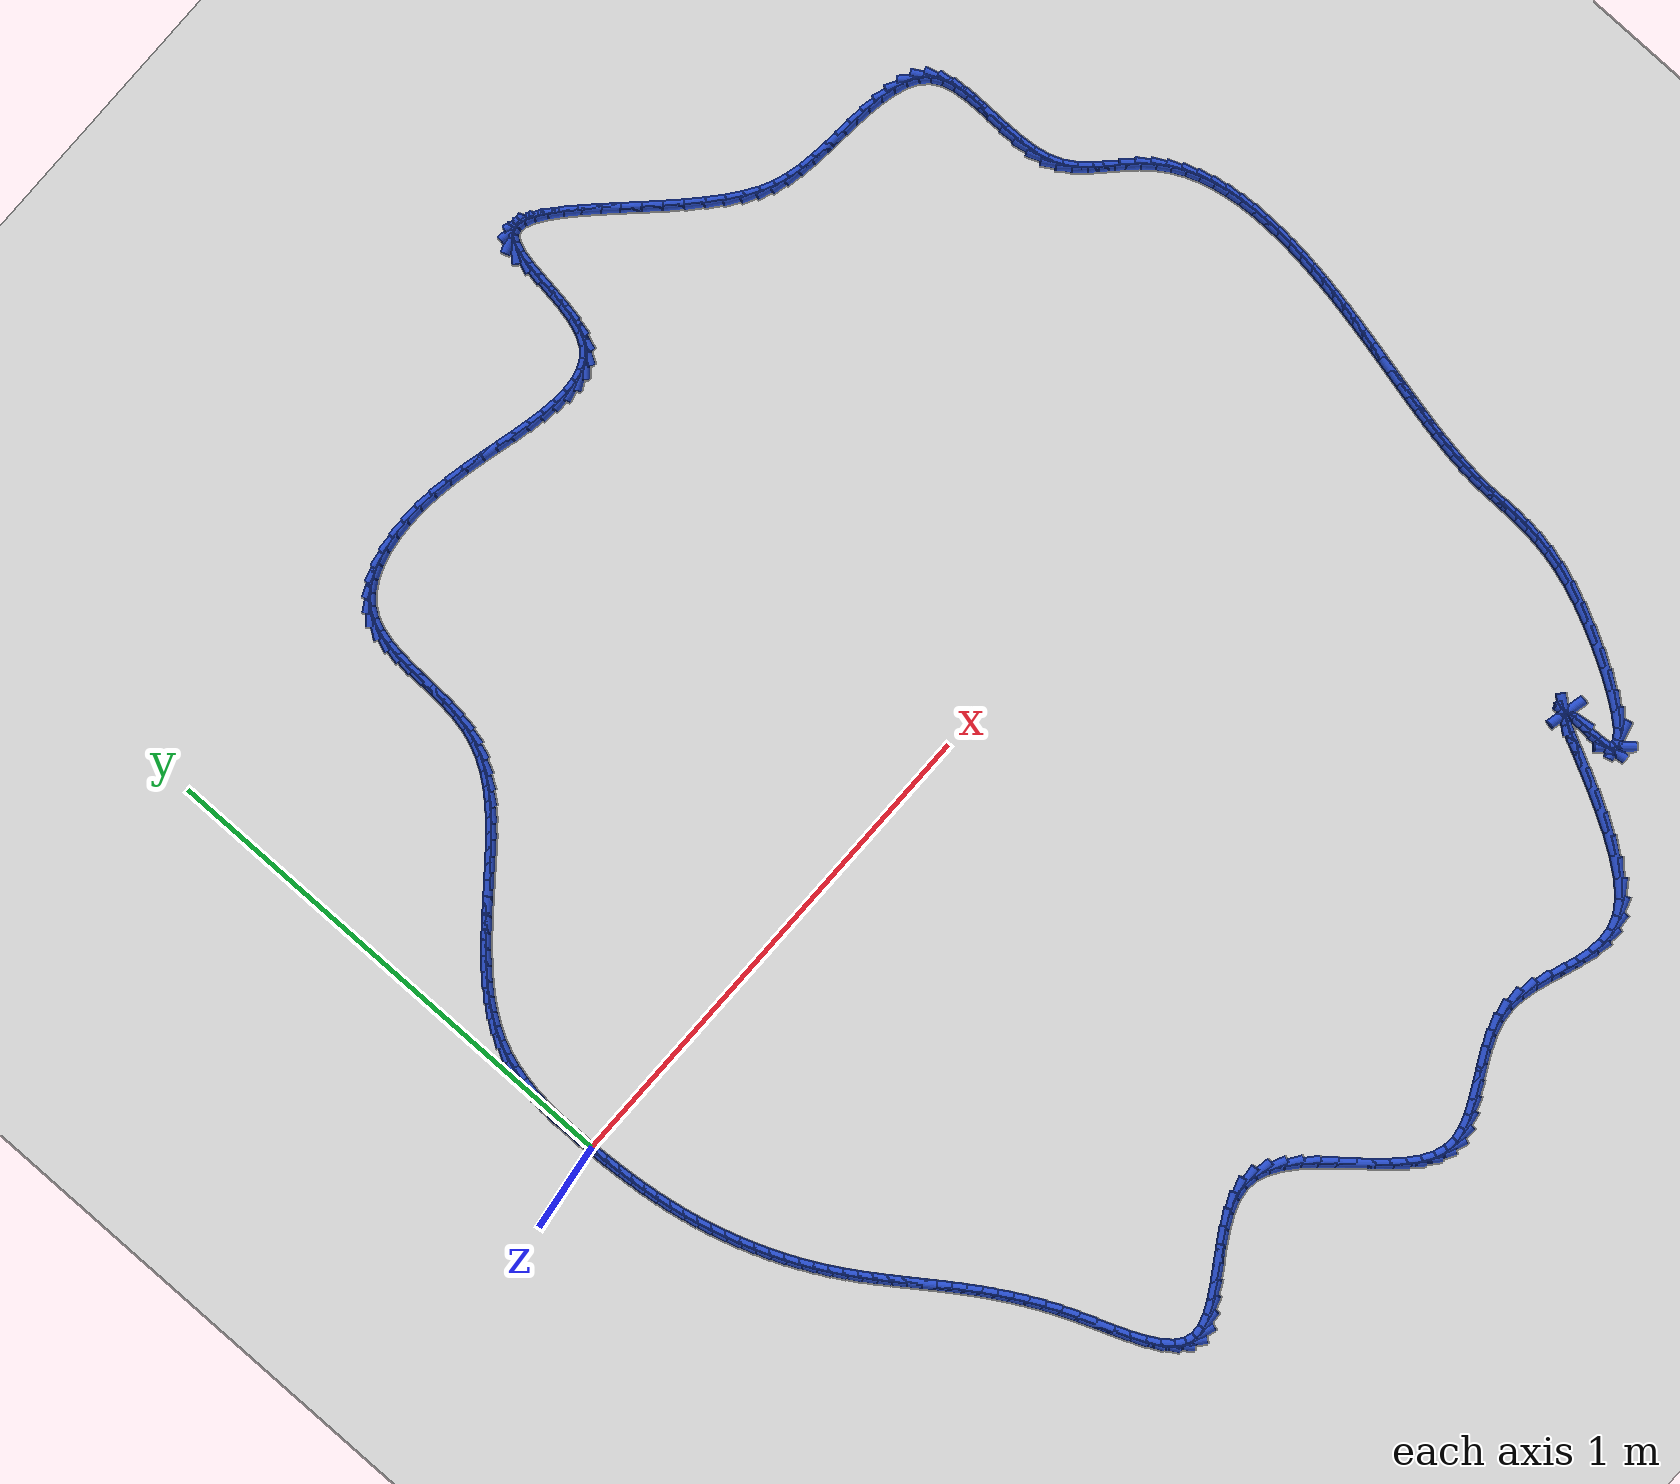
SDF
<sdf version="1.6">
 <world name="default">
  <light name="sun" type="directional">
   <pose>0 0 10 0 -0 0</pose>
   <diffuse>0.8 0.8 0.8 1</diffuse>
   <specular>0.2 0.2 0.2 1</specular>
   <attenuation>
    <range>1000</range>
    <constant>0.9</constant>
    <linear>0.01</linear>
    <quadratic>0.001</quadratic>
   </attenuation>
   <direction>-0.5 0.1 -0.9</direction>
  </light>
  <model name="ground_plane">
   <static>1</static>
   <link name="link">
    <collision name="collision">
     <geometry><plane><normal>0 0 1</normal><size>100 100</size></plane></geometry>
     <surface><friction><ode><mu>100</mu><mu2>50</mu2></ode></friction></surface>
    </collision>
    <visual name="visual">
     <cast_shadows>0</cast_shadows>
     <geometry><plane><normal>0 0 1</normal><size>100 100</size></plane></geometry>
     <material>
      <script><uri>file://media/materials/scripts/gazebo.material</uri><name>Gazebo/WhiteGlow</name></script>
     </material>
    </visual>
   </link>
  </model>
  <gravity>0 0 -9.8</gravity>
  <magnetic_field>6e-06 2.3e-05 -4.2e-05</magnetic_field>
  <atmosphere type="adiabatic"/>
  <physics name="default_physics" default="0" type="ode">
   <max_step_size>0.001</max_step_size>
   <real_time_factor>1</real_time_factor>
   <real_time_update_rate>1000</real_time_update_rate>
  </physics>
  <scene><ambient>0.4 0.4 0.4 1</ambient><background>0.7 0.7 0.7 1</background><shadows>1</shadows></scene>
  <spherical_coordinates>
   <surface_model>EARTH_WGS84</surface_model>
   <latitude_deg>0</latitude_deg>
   <longitude_deg>0</longitude_deg>
   <elevation>0</elevation>
   <heading_deg>0</heading_deg>
  </spherical_coordinates>
  <model name="line">
   <link name="link_0">
    <pose>-1.1872013788716274e-17 2.0816681711721685e-17 0.01 0 1.57 -1.5451109101170222</pose>
    <collision name="collision">
     <geometry><cylinder><radius>0.01</radius><length>0.08</length></cylinder></geometry>
    </collision>
    <visual name="visual">
     <material>
      <script><name>Gazebo/Blue</name><uri>file://media/materials/scripts/gazebo.material</uri></script>
     </material>
     <geometry><cylinder><radius>0.01</radius><length>0.08</length></cylinder></geometry>
    </visual>
   </link>
   <link name="link_1">
    <pose>-0.0007698900590970052 0.02996722817668123 0.01 0 1.57 -1.5673495071454218</pose>
    <collision name="collision">
     <geometry><cylinder><radius>0.01</radius><length>0.08</length></cylinder></geometry>
    </collision>
    <visual name="visual">
     <material>
      <script><name>Gazebo/Blue</name><uri>file://media/materials/scripts/gazebo.material</uri></script>
     </material>
     <geometry><cylinder><radius>0.01</radius><length>0.08</length></cylinder></geometry>
    </visual>
   </link>
   <link name="link_2">
    <pose>-0.0008736150124650972 0.060060053779899154 0.01 0 1.57 1.5438950808368137</pose>
    <collision name="collision">
     <geometry><cylinder><radius>0.01</radius><length>0.08</length></cylinder></geometry>
    </collision>
    <visual name="visual">
     <material>
      <script><name>Gazebo/Blue</name><uri>file://media/materials/scripts/gazebo.material</uri></script>
     </material>
     <geometry><cylinder><radius>0.01</radius><length>0.08</length></cylinder></geometry>
    </visual>
   </link>
   <link name="link_3">
    <pose>-6.574774106356956e-05 0.09008365881764162 0.01 0 1.57 1.5048666415744176</pose>
    <collision name="collision">
     <geometry><cylinder><radius>0.01</radius><length>0.08</length></cylinder></geometry>
    </collision>
    <visual name="visual">
     <material>
      <script><name>Gazebo/Blue</name><uri>file://media/materials/scripts/gazebo.material</uri></script>
     </material>
     <geometry><cylinder><radius>0.01</radius><length>0.08</length></cylinder></geometry>
    </visual>
   </link>
   <link name="link_4">
    <pose>0.001899138874148295 0.11984322529789647 0.01 0 1.57 1.45637503997327</pose>
    <collision name="collision">
     <geometry><cylinder><radius>0.01</radius><length>0.08</length></cylinder></geometry>
    </collision>
    <visual name="visual">
     <material>
      <script><name>Gazebo/Blue</name><uri>file://media/materials/scripts/gazebo.material</uri></script>
     </material>
     <geometry><cylinder><radius>0.01</radius><length>0.08</length></cylinder></geometry>
    </visual>
   </link>
   <link name="link_5">
    <pose>0.005266471952211213 0.1491439352286515 0.01 0 1.57 1.3974837513793676</pose>
    <collision name="collision">
     <geometry><cylinder><radius>0.01</radius><length>0.08</length></cylinder></geometry>
    </collision>
    <visual name="visual">
     <material>
      <script><name>Gazebo/Blue</name><uri>file://media/materials/scripts/gazebo.material</uri></script>
     </material>
     <geometry><cylinder><radius>0.01</radius><length>0.08</length></cylinder></geometry>
    </visual>
   </link>
   <link name="link_6">
    <pose>0.0102816786121659 0.17779097061789453 0.01 0 1.57 1.3272106321210706</pose>
    <collision name="collision">
     <geometry><cylinder><radius>0.01</radius><length>0.08</length></cylinder></geometry>
    </collision>
    <visual name="visual">
     <material>
      <script><name>Gazebo/Blue</name><uri>file://media/materials/scripts/gazebo.material</uri></script>
     </material>
     <geometry><cylinder><radius>0.01</radius><length>0.08</length></cylinder></geometry>
    </visual>
   </link>
   <link name="link_7">
    <pose>0.01719018597305308 0.20558951347361348 0.01 0 1.57 1.2447186185263812</pose>
    <collision name="collision">
     <geometry><cylinder><radius>0.01</radius><length>0.08</length></cylinder></geometry>
    </collision>
    <visual name="visual">
     <material>
      <script><name>Gazebo/Blue</name><uri>file://media/materials/scripts/gazebo.material</uri></script>
     </material>
     <geometry><cylinder><radius>0.01</radius><length>0.08</length></cylinder></geometry>
    </visual>
   </link>
   <link name="link_8">
    <pose>0.026237421153913462 0.23234474580379605 0.01 0 1.57 1.1509238718050745</pose>
    <collision name="collision">
     <geometry><cylinder><radius>0.01</radius><length>0.08</length></cylinder></geometry>
    </collision>
    <visual name="visual">
     <material>
      <script><name>Gazebo/Blue</name><uri>file://media/materials/scripts/gazebo.material</uri></script>
     </material>
     <geometry><cylinder><radius>0.01</radius><length>0.08</length></cylinder></geometry>
    </visual>
   </link>
   <link name="link_9">
    <pose>0.03763806938680644 0.2578827125401909 0.01 0 1.57 1.0586166648460742</pose>
    <collision name="collision">
     <geometry><cylinder><radius>0.01</radius><length>0.08</length></cylinder></geometry>
    </collision>
    <visual name="visual">
     <material>
      <script><name>Gazebo/Blue</name><uri>file://media/materials/scripts/gazebo.material</uri></script>
     </material>
     <geometry><cylinder><radius>0.01</radius><length>0.08</length></cylinder></geometry>
    </visual>
   </link>
   <link name="link_10">
    <pose>0.051322447408647644 0.2822224447587526 0.01 0 1.57 0.9758450162834615</pose>
    <collision name="collision">
     <geometry><cylinder><radius>0.01</radius><length>0.08</length></cylinder></geometry>
    </collision>
    <visual name="visual">
     <material>
      <script><name>Gazebo/Blue</name><uri>file://media/materials/scripts/gazebo.material</uri></script>
     </material>
     <geometry><cylinder><radius>0.01</radius><length>0.08</length></cylinder></geometry>
    </visual>
   </link>
   <link name="link_11">
    <pose>0.06706701228580245 0.30548739011137616 0.01 0 1.57 0.9035324256831487</pose>
    <collision name="collision">
     <geometry><cylinder><radius>0.01</radius><length>0.08</length></cylinder></geometry>
    </collision>
    <visual name="visual">
     <material>
      <script><name>Gazebo/Blue</name><uri>file://media/materials/scripts/gazebo.material</uri></script>
     </material>
     <geometry><cylinder><radius>0.01</radius><length>0.08</length></cylinder></geometry>
    </visual>
   </link>
   <link name="link_12">
    <pose>0.08464670987519629 0.3278020218294001 0.01 0 1.57 0.841854725073762</pose>
    <collision name="collision">
     <geometry><cylinder><radius>0.01</radius><length>0.08</length></cylinder></geometry>
    </collision>
    <visual name="visual">
     <material>
      <script><name>Gazebo/Blue</name><uri>file://media/materials/scripts/gazebo.material</uri></script>
     </material>
     <geometry><cylinder><radius>0.01</radius><length>0.08</length></cylinder></geometry>
    </visual>
   </link>
   <link name="link_13">
    <pose>0.10383648603375471 0.34929081314416266 0.01 0 1.57 0.7905386433102758</pose>
    <collision name="collision">
     <geometry><cylinder><radius>0.01</radius><length>0.08</length></cylinder></geometry>
    </collision>
    <visual name="visual">
     <material>
      <script><name>Gazebo/Blue</name><uri>file://media/materials/scripts/gazebo.material</uri></script>
     </material>
     <geometry><cylinder><radius>0.01</radius><length>0.08</length></cylinder></geometry>
    </visual>
   </link>
   <link name="link_14">
    <pose>0.12441128661840307 0.37007823728700195 0.01 0 1.57 0.7490753755160869</pose>
    <collision name="collision">
     <geometry><cylinder><radius>0.01</radius><length>0.08</length></cylinder></geometry>
    </collision>
    <visual name="visual">
     <material>
      <script><name>Gazebo/Blue</name><uri>file://media/materials/scripts/gazebo.material</uri></script>
     </material>
     <geometry><cylinder><radius>0.01</radius><length>0.08</length></cylinder></geometry>
    </visual>
   </link>
   <link name="link_15">
    <pose>0.14614605748606693 0.39028876748925656 0.01 0 1.57 0.7168812915747746</pose>
    <collision name="collision">
     <geometry><cylinder><radius>0.01</radius><length>0.08</length></cylinder></geometry>
    </collision>
    <visual name="visual">
     <material>
      <script><name>Gazebo/Blue</name><uri>file://media/materials/scripts/gazebo.material</uri></script>
     </material>
     <geometry><cylinder><radius>0.01</radius><length>0.08</length></cylinder></geometry>
    </visual>
   </link>
   <link name="link_16">
    <pose>0.16881574449367168 0.41004687698226455 0.01 0 1.57 0.6934040923392459</pose>
    <collision name="collision">
     <geometry><cylinder><radius>0.01</radius><length>0.08</length></cylinder></geometry>
    </collision>
    <visual name="visual">
     <material>
      <script><name>Gazebo/Blue</name><uri>file://media/materials/scripts/gazebo.material</uri></script>
     </material>
     <geometry><cylinder><radius>0.01</radius><length>0.08</length></cylinder></geometry>
    </visual>
   </link>
   <link name="link_17">
    <pose>0.1921952934981428 0.42947703899736434 0.01 0 1.57 0.6781859495157794</pose>
    <collision name="collision">
     <geometry><cylinder><radius>0.01</radius><length>0.08</length></cylinder></geometry>
    </collision>
    <visual name="visual">
     <material>
      <script><name>Gazebo/Blue</name><uri>file://media/materials/scripts/gazebo.material</uri></script>
     </material>
     <geometry><cylinder><radius>0.01</radius><length>0.08</length></cylinder></geometry>
    </visual>
   </link>
   <link name="link_18">
    <pose>0.21605965035640579 0.44870372676589415 0.01 0 1.57 0.6708973248589045</pose>
    <collision name="collision">
     <geometry><cylinder><radius>0.01</radius><length>0.08</length></cylinder></geometry>
    </collision>
    <visual name="visual">
     <material>
      <script><name>Gazebo/Blue</name><uri>file://media/materials/scripts/gazebo.material</uri></script>
     </material>
     <geometry><cylinder><radius>0.01</radius><length>0.08</length></cylinder></geometry>
    </visual>
   </link>
   <link name="link_19">
    <pose>0.24018376092538607 0.4678514135191925 0.01 0 1.57 0.6713525008368391</pose>
    <collision name="collision">
     <geometry><cylinder><radius>0.01</radius><length>0.08</length></cylinder></geometry>
    </collision>
    <visual name="visual">
     <material>
      <script><name>Gazebo/Blue</name><uri>file://media/materials/scripts/gazebo.material</uri></script>
     </material>
     <geometry><cylinder><radius>0.01</radius><length>0.08</length></cylinder></geometry>
    </visual>
   </link>
   <link name="link_20">
    <pose>0.26434257106200904 0.4870445724885972 0.01 0 1.57 0.6798132465846809</pose>
    <collision name="collision">
     <geometry><cylinder><radius>0.01</radius><length>0.08</length></cylinder></geometry>
    </collision>
    <visual name="visual">
     <material>
      <script><name>Gazebo/Blue</name><uri>file://media/materials/scripts/gazebo.material</uri></script>
     </material>
     <geometry><cylinder><radius>0.01</radius><length>0.08</length></cylinder></geometry>
    </visual>
   </link>
   <link name="link_21">
    <pose>0.28830198507840205 0.5064122257639235 0.01 0 1.57 0.6994442417516715</pose>
    <collision name="collision">
     <geometry><cylinder><radius>0.01</radius><length>0.08</length></cylinder></geometry>
    </collision>
    <visual name="visual">
     <material>
      <script><name>Gazebo/Blue</name><uri>file://media/materials/scripts/gazebo.material</uri></script>
     </material>
     <geometry><cylinder><radius>0.01</radius><length>0.08</length></cylinder></geometry>
    </visual>
   </link>
   <link name="link_22">
    <pose>0.31173708832156377 0.5261290870317821 0.01 0 1.57 0.7324984477223815</pose>
    <collision name="collision">
     <geometry><cylinder><radius>0.01</radius><length>0.08</length></cylinder></geometry>
    </collision>
    <visual name="visual">
     <material>
      <script><name>Gazebo/Blue</name><uri>file://media/materials/scripts/gazebo.material</uri></script>
     </material>
     <geometry><cylinder><radius>0.01</radius><length>0.08</length></cylinder></geometry>
    </visual>
   </link>
   <link name="link_23">
    <pose>0.3342705140392098 0.5463962589622757 0.01 0 1.57 0.7798428348184872</pose>
    <collision name="collision">
     <geometry><cylinder><radius>0.01</radius><length>0.08</length></cylinder></geometry>
    </collision>
    <visual name="visual">
     <material>
      <script><name>Gazebo/Blue</name><uri>file://media/materials/scripts/gazebo.material</uri></script>
     </material>
     <geometry><cylinder><radius>0.01</radius><length>0.08</length></cylinder></geometry>
    </visual>
   </link>
   <link name="link_24">
    <pose>0.3555242599318217 0.5674151639733479 0.01 0 1.57 0.8424951398362368</pose>
    <collision name="collision">
     <geometry><cylinder><radius>0.01</radius><length>0.08</length></cylinder></geometry>
    </collision>
    <visual name="visual">
     <material>
      <script><name>Gazebo/Blue</name><uri>file://media/materials/scripts/gazebo.material</uri></script>
     </material>
     <geometry><cylinder><radius>0.01</radius><length>0.08</length></cylinder></geometry>
    </visual>
   </link>
   <link name="link_25">
    <pose>0.37512032369988113 0.5893872244829423 0.01 0 1.57 0.921360885873998</pose>
    <collision name="collision">
     <geometry><cylinder><radius>0.01</radius><length>0.08</length></cylinder></geometry>
    </collision>
    <visual name="visual">
     <material>
      <script><name>Gazebo/Blue</name><uri>file://media/materials/scripts/gazebo.material</uri></script>
     </material>
     <geometry><cylinder><radius>0.01</radius><length>0.08</length></cylinder></geometry>
    </visual>
   </link>
   <link name="link_26">
    <pose>0.3926807030438695 0.6125138629090023 0.01 0 1.57 1.0167613303036338</pose>
    <collision name="collision">
     <geometry><cylinder><radius>0.01</radius><length>0.08</length></cylinder></geometry>
    </collision>
    <visual name="visual">
     <material>
      <script><name>Gazebo/Blue</name><uri>file://media/materials/scripts/gazebo.material</uri></script>
     </material>
     <geometry><cylinder><radius>0.01</radius><length>0.08</length></cylinder></geometry>
    </visual>
   </link>
   <link name="link_27">
    <pose>0.4078273956642686 0.6369965016694712 0.01 0 1.57 1.127787545279394</pose>
    <collision name="collision">
     <geometry><cylinder><radius>0.01</radius><length>0.08</length></cylinder></geometry>
    </collision>
    <visual name="visual">
     <material>
      <script><name>Gazebo/Blue</name><uri>file://media/materials/scripts/gazebo.material</uri></script>
     </material>
     <geometry><cylinder><radius>0.01</radius><length>0.08</length></cylinder></geometry>
    </visual>
   </link>
   <link name="link_28">
    <pose>0.4201823992615598 0.6630365631822922 0.01 0 1.57 1.2515728648714242</pose>
    <collision name="collision">
     <geometry><cylinder><radius>0.01</radius><length>0.08</length></cylinder></geometry>
    </collision>
    <visual name="visual">
     <material>
      <script><name>Gazebo/Blue</name><uri>file://media/materials/scripts/gazebo.material</uri></script>
     </material>
     <geometry><cylinder><radius>0.01</radius><length>0.08</length></cylinder></geometry>
    </visual>
   </link>
   <link name="link_29">
    <pose>0.42937019553111067 0.6908339102998016 0.01 0 1.57 1.3698600469503874</pose>
    <collision name="collision">
     <geometry><cylinder><radius>0.01</radius><length>0.08</length></cylinder></geometry>
    </collision>
    <visual name="visual">
     <material>
      <script><name>Gazebo/Blue</name><uri>file://media/materials/scripts/gazebo.material</uri></script>
     </material>
     <geometry><cylinder><radius>0.01</radius><length>0.08</length></cylinder></geometry>
    </visual>
   </link>
   <link name="link_30">
    <pose>0.4353836315976691 0.7203571292086329 0.01 0 1.57 1.4546445446378071</pose>
    <collision name="collision">
     <geometry><cylinder><radius>0.01</radius><length>0.08</length></cylinder></geometry>
    </collision>
    <visual name="visual">
     <material>
      <script><name>Gazebo/Blue</name><uri>file://media/materials/scripts/gazebo.material</uri></script>
     </material>
     <geometry><cylinder><radius>0.01</radius><length>0.08</length></cylinder></geometry>
    </visual>
   </link>
   <link name="link_31">
    <pose>0.43897069717066817 0.7511006930403253 0.01 0 1.57 1.5071485653790522</pose>
    <collision name="collision">
     <geometry><cylinder><radius>0.01</radius><length>0.08</length></cylinder></geometry>
    </collision>
    <visual name="visual">
     <material>
      <script><name>Gazebo/Blue</name><uri>file://media/materials/scripts/gazebo.material</uri></script>
     </material>
     <geometry><cylinder><radius>0.01</radius><length>0.08</length></cylinder></geometry>
    </visual>
   </link>
   <link name="link_32">
    <pose>0.440971956508509 0.7825009523901908 0.01 0 1.57 1.5309354088474274</pose>
    <collision name="collision">
     <geometry><cylinder><radius>0.01</radius><length>0.08</length></cylinder></geometry>
    </collision>
    <visual name="visual">
     <material>
      <script><name>Gazebo/Blue</name><uri>file://media/materials/scripts/gazebo.material</uri></script>
     </material>
     <geometry><cylinder><radius>0.01</radius><length>0.08</length></cylinder></geometry>
    </visual>
   </link>
   <link name="link_33">
    <pose>0.4422279738695924 0.8139942578535415 0.01 0 1.57 1.5272641448382829</pose>
    <collision name="collision">
     <geometry><cylinder><radius>0.01</radius><length>0.08</length></cylinder></geometry>
    </collision>
    <visual name="visual">
     <material>
      <script><name>Gazebo/Blue</name><uri>file://media/materials/scripts/gazebo.material</uri></script>
     </material>
     <geometry><cylinder><radius>0.01</radius><length>0.08</length></cylinder></geometry>
    </visual>
   </link>
   <link name="link_34">
    <pose>0.4435793135123191 0.8450169600256893 0.01 0 1.57 1.4946734663981884</pose>
    <collision name="collision">
     <geometry><cylinder><radius>0.01</radius><length>0.08</length></cylinder></geometry>
    </collision>
    <visual name="visual">
     <material>
      <script><name>Gazebo/Blue</name><uri>file://media/materials/scripts/gazebo.material</uri></script>
     </material>
     <geometry><cylinder><radius>0.01</radius><length>0.08</length></cylinder></geometry>
    </visual>
   </link>
   <link name="link_35">
    <pose>0.44586653969509 0.8750054095019463 0.01 0 1.57 1.4286271214535384</pose>
    <collision name="collision">
     <geometry><cylinder><radius>0.01</radius><length>0.08</length></cylinder></geometry>
    </collision>
    <visual name="visual">
     <material>
      <script><name>Gazebo/Blue</name><uri>file://media/materials/scripts/gazebo.material</uri></script>
     </material>
     <geometry><cylinder><radius>0.01</radius><length>0.08</length></cylinder></geometry>
    </visual>
   </link>
   <link name="link_36">
    <pose>0.4499302166763056 0.9033959568776234 0.01 0 1.57 1.3213930779234753</pose>
    <collision name="collision">
     <geometry><cylinder><radius>0.01</radius><length>0.08</length></cylinder></geometry>
    </collision>
    <visual name="visual">
     <material>
      <script><name>Gazebo/Blue</name><uri>file://media/materials/scripts/gazebo.material</uri></script>
     </material>
     <geometry><cylinder><radius>0.01</radius><length>0.08</length></cylinder></geometry>
    </visual>
   </link>
   <link name="link_37">
    <pose>0.45661090871436694 0.9296249527480335 0.01 0 1.57 1.1635627403228734</pose>
    <collision name="collision">
     <geometry><cylinder><radius>0.01</radius><length>0.08</length></cylinder></geometry>
    </collision>
    <visual name="visual">
     <material>
      <script><name>Gazebo/Blue</name><uri>file://media/materials/scripts/gazebo.material</uri></script>
     </material>
     <geometry><cylinder><radius>0.01</radius><length>0.08</length></cylinder></geometry>
    </visual>
   </link>
   <link name="link_38">
    <pose>0.46674918006767485 0.9531287477084887 0.01 0 1.57 0.9526135646859881</pose>
    <collision name="collision">
     <geometry><cylinder><radius>0.01</radius><length>0.08</length></cylinder></geometry>
    </collision>
    <visual name="visual">
     <material>
      <script><name>Gazebo/Blue</name><uri>file://media/materials/scripts/gazebo.material</uri></script>
     </material>
     <geometry><cylinder><radius>0.01</radius><length>0.08</length></cylinder></geometry>
    </visual>
   </link>
   <link name="link_39">
    <pose>0.4811420381584736 0.9733670530089876 0.01 0 1.57 0.7309356425136097</pose>
    <collision name="collision">
     <geometry><cylinder><radius>0.01</radius><length>0.08</length></cylinder></geometry>
    </collision>
    <visual name="visual">
     <material>
      <script><name>Gazebo/Blue</name><uri>file://media/materials/scripts/gazebo.material</uri></script>
     </material>
     <geometry><cylinder><radius>0.01</radius><length>0.08</length></cylinder></geometry>
    </visual>
   </link>
   <link name="link_40">
    <pose>0.49988761090628964 0.9901744070029517 0.01 0 1.57 0.5382414222113716</pose>
    <collision name="collision">
     <geometry><cylinder><radius>0.01</radius><length>0.08</length></cylinder></geometry>
    </collision>
    <visual name="visual">
     <material>
      <script><name>Gazebo/Blue</name><uri>file://media/materials/scripts/gazebo.material</uri></script>
     </material>
     <geometry><cylinder><radius>0.01</radius><length>0.08</length></cylinder></geometry>
    </visual>
   </link>
   <link name="link_41">
    <pose>0.5225208499953237 1.0036873939847466 0.01 0 1.57 0.3787790663361529</pose>
    <collision name="collision">
     <geometry><cylinder><radius>0.01</radius><length>0.08</length></cylinder></geometry>
    </collision>
    <visual name="visual">
     <material>
      <script><name>Gazebo/Blue</name><uri>file://media/materials/scripts/gazebo.material</uri></script>
     </material>
     <geometry><cylinder><radius>0.01</radius><length>0.08</length></cylinder></geometry>
    </visual>
   </link>
   <link name="link_42">
    <pose>0.5485606880715946 1.0140511896720912 0.01 0 1.57 0.24882336007840214</pose>
    <collision name="collision">
     <geometry><cylinder><radius>0.01</radius><length>0.08</length></cylinder></geometry>
    </collision>
    <visual name="visual">
     <material>
      <script><name>Gazebo/Blue</name><uri>file://media/materials/scripts/gazebo.material</uri></script>
     </material>
     <geometry><cylinder><radius>0.01</radius><length>0.08</length></cylinder></geometry>
    </visual>
   </link>
   <link name="link_43">
    <pose>0.5775260577811204 1.0214109697827043 0.01 0 1.57 0.14232825245619285</pose>
    <collision name="collision">
     <geometry><cylinder><radius>0.01</radius><length>0.08</length></cylinder></geometry>
    </collision>
    <visual name="visual">
     <material>
      <script><name>Gazebo/Blue</name><uri>file://media/materials/scripts/gazebo.material</uri></script>
     </material>
     <geometry><cylinder><radius>0.01</radius><length>0.08</length></cylinder></geometry>
    </visual>
   </link>
   <link name="link_44">
    <pose>0.6089358917699195 1.0259119100343048 0.01 0 1.57 0.0535030720630858</pose>
    <collision name="collision">
     <geometry><cylinder><radius>0.01</radius><length>0.08</length></cylinder></geometry>
    </collision>
    <visual name="visual">
     <material>
      <script><name>Gazebo/Blue</name><uri>file://media/materials/scripts/gazebo.material</uri></script>
     </material>
     <geometry><cylinder><radius>0.01</radius><length>0.08</length></cylinder></geometry>
    </visual>
   </link>
   <link name="link_45">
    <pose>0.6423091226840105 1.0276991861446123 0.01 0 1.57 -0.02240909431755699</pose>
    <collision name="collision">
     <geometry><cylinder><radius>0.01</radius><length>0.08</length></cylinder></geometry>
    </collision>
    <visual name="visual">
     <material>
      <script><name>Gazebo/Blue</name><uri>file://media/materials/scripts/gazebo.material</uri></script>
     </material>
     <geometry><cylinder><radius>0.01</radius><length>0.08</length></cylinder></geometry>
    </visual>
   </link>
   <link name="link_46">
    <pose>0.677164683169412 1.0269179738313454 0.01 0 1.57 -0.08913322253763291</pose>
    <collision name="collision">
     <geometry><cylinder><radius>0.01</radius><length>0.08</length></cylinder></geometry>
    </collision>
    <visual name="visual">
     <material>
      <script><name>Gazebo/Blue</name><uri>file://media/materials/scripts/gazebo.material</uri></script>
     </material>
     <geometry><cylinder><radius>0.01</radius><length>0.08</length></cylinder></geometry>
    </visual>
   </link>
   <link name="link_47">
    <pose>0.7130215058721426 1.023713448812224 0.01 0 1.57 -0.14889320953594515</pose>
    <collision name="collision">
     <geometry><cylinder><radius>0.01</radius><length>0.08</length></cylinder></geometry>
    </collision>
    <visual name="visual">
     <material>
      <script><name>Gazebo/Blue</name><uri>file://media/materials/scripts/gazebo.material</uri></script>
     </material>
     <geometry><cylinder><radius>0.01</radius><length>0.08</length></cylinder></geometry>
    </visual>
   </link>
   <link name="link_48">
    <pose>0.7494063517024228 1.018255600582526 0.01 0 1.57 -0.19597598391370843</pose>
    <collision name="collision">
     <geometry><cylinder><radius>0.01</radius><length>0.08</length></cylinder></geometry>
    </collision>
    <visual name="visual">
     <material>
      <script><name>Gazebo/Blue</name><uri>file://media/materials/scripts/gazebo.material</uri></script>
     </material>
     <geometry><cylinder><radius>0.01</radius><length>0.08</length></cylinder></geometry>
    </visual>
   </link>
   <link name="link_49">
    <pose>0.7859371371921492 1.0110033607658349 0.01 0 1.57 -0.22710652442872728</pose>
    <collision name="collision">
     <geometry><cylinder><radius>0.01</radius><length>0.08</length></cylinder></geometry>
    </collision>
    <visual name="visual">
     <material>
      <script><name>Gazebo/Blue</name><uri>file://media/materials/scripts/gazebo.material</uri></script>
     </material>
     <geometry><cylinder><radius>0.01</radius><length>0.08</length></cylinder></geometry>
    </visual>
   </link>
   <link name="link_50">
    <pose>0.8222906612316994 1.002602304372791 0.01 0 1.57 -0.24334169820185125</pose>
    <collision name="collision">
     <geometry><cylinder><radius>0.01</radius><length>0.08</length></cylinder></geometry>
    </collision>
    <visual name="visual">
     <material>
      <script><name>Gazebo/Blue</name><uri>file://media/materials/scripts/gazebo.material</uri></script>
     </material>
     <geometry><cylinder><radius>0.01</radius><length>0.08</length></cylinder></geometry>
    </visual>
   </link>
   <link name="link_51">
    <pose>0.8581447073365691 0.9937011274467502 0.01 0 1.57 -0.24483125765413086</pose>
    <collision name="collision">
     <geometry><cylinder><radius>0.01</radius><length>0.08</length></cylinder></geometry>
    </collision>
    <visual name="visual">
     <material>
      <script><name>Gazebo/Blue</name><uri>file://media/materials/scripts/gazebo.material</uri></script>
     </material>
     <geometry><cylinder><radius>0.01</radius><length>0.08</length></cylinder></geometry>
    </visual>
   </link>
   <link name="link_52">
    <pose>0.8931770590222533 0.9849485260310674 0.01 0 1.57 -0.23057554519354578</pose>
    <collision name="collision">
     <geometry><cylinder><radius>0.01</radius><length>0.08</length></cylinder></geometry>
    </collision>
    <visual name="visual">
     <material>
      <script><name>Gazebo/Blue</name><uri>file://media/materials/scripts/gazebo.material</uri></script>
     </material>
     <geometry><cylinder><radius>0.01</radius><length>0.08</length></cylinder></geometry>
    </visual>
   </link>
   <link name="link_53">
    <pose>0.927065499804249 0.9769931961690989 0.01 0 1.57 -0.19813388995301978</pose>
    <collision name="collision">
     <geometry><cylinder><radius>0.01</radius><length>0.08</length></cylinder></geometry>
    </collision>
    <visual name="visual">
     <material>
      <script><name>Gazebo/Blue</name><uri>file://media/materials/scripts/gazebo.material</uri></script>
     </material>
     <geometry><cylinder><radius>0.01</radius><length>0.08</length></cylinder></geometry>
    </visual>
   </link>
   <link name="link_54">
    <pose>0.9594878131980513 0.9704838339041993 0.01 0 1.57 -0.14312583075689134</pose>
    <collision name="collision">
     <geometry><cylinder><radius>0.01</radius><length>0.08</length></cylinder></geometry>
    </collision>
    <visual name="visual">
     <material>
      <script><name>Gazebo/Blue</name><uri>file://media/materials/scripts/gazebo.material</uri></script>
     </material>
     <geometry><cylinder><radius>0.01</radius><length>0.08</length></cylinder></geometry>
    </visual>
   </link>
   <link name="link_55">
    <pose>0.9901217827191567 0.966069135279725 0.01 0 1.57 -0.05852842001810809</pose>
    <collision name="collision">
     <geometry><cylinder><radius>0.01</radius><length>0.08</length></cylinder></geometry>
    </collision>
    <visual name="visual">
     <material>
      <script><name>Gazebo/Blue</name><uri>file://media/materials/scripts/gazebo.material</uri></script>
     </material>
     <geometry><cylinder><radius>0.01</radius><length>0.08</length></cylinder></geometry>
    </visual>
   </link>
   <link name="link_56">
    <pose>1.0186451918830601 0.964397796339031 0.01 0 1.57 0.06585614501446807</pose>
    <collision name="collision">
     <geometry><cylinder><radius>0.01</radius><length>0.08</length></cylinder></geometry>
    </collision>
    <visual name="visual">
     <material>
      <script><name>Gazebo/Blue</name><uri>file://media/materials/scripts/gazebo.material</uri></script>
     </material>
     <geometry><cylinder><radius>0.01</radius><length>0.08</length></cylinder></geometry>
    </visual>
   </link>
   <link name="link_57">
    <pose>1.0447358242052582 0.966118513125473 0.01 0 1.57 0.24205482684594376</pose>
    <collision name="collision">
     <geometry><cylinder><radius>0.01</radius><length>0.08</length></cylinder></geometry>
    </collision>
    <visual name="visual">
     <material>
      <script><name>Gazebo/Blue</name><uri>file://media/materials/scripts/gazebo.material</uri></script>
     </material>
     <geometry><cylinder><radius>0.01</radius><length>0.08</length></cylinder></geometry>
    </visual>
   </link>
   <link name="link_58">
    <pose>1.0680714632012465 0.9718799816824066 0.01 0 1.57 0.4762706710339979</pose>
    <collision name="collision">
     <geometry><cylinder><radius>0.01</radius><length>0.08</length></cylinder></geometry>
    </collision>
    <visual name="visual">
     <material>
      <script><name>Gazebo/Blue</name><uri>file://media/materials/scripts/gazebo.material</uri></script>
     </material>
     <geometry><cylinder><radius>0.01</radius><length>0.08</length></cylinder></geometry>
    </visual>
   </link>
   <link name="link_59">
    <pose>1.0883298923865208 0.9823308980531876 0.01 0 1.57 0.7526378779338351</pose>
    <collision name="collision">
     <geometry><cylinder><radius>0.01</radius><length>0.08</length></cylinder></geometry>
    </collision>
    <visual name="visual">
     <material>
      <script><name>Gazebo/Blue</name><uri>file://media/materials/scripts/gazebo.material</uri></script>
     </material>
     <geometry><cylinder><radius>0.01</radius><length>0.08</length></cylinder></geometry>
    </visual>
   </link>
   <link name="link_60">
    <pose>1.105188895276577 0.9981199582811707 0.01 0 1.57 1.0275307649152405</pose>
    <collision name="collision">
     <geometry><cylinder><radius>0.01</radius><length>0.08</length></cylinder></geometry>
    </collision>
    <visual name="visual">
     <material>
      <script><name>Gazebo/Blue</name><uri>file://media/materials/scripts/gazebo.material</uri></script>
     </material>
     <geometry><cylinder><radius>0.01</radius><length>0.08</length></cylinder></geometry>
    </visual>
   </link>
   <link name="link_61">
    <pose>1.118331832248215 1.019884209910793 0.01 0 1.57 1.2358446032262782</pose>
    <collision name="collision">
     <geometry><cylinder><radius>0.01</radius><length>0.08</length></cylinder></geometry>
    </collision>
    <visual name="visual">
     <material>
      <script><name>Gazebo/Blue</name><uri>file://media/materials/scripts/gazebo.material</uri></script>
     </material>
     <geometry><cylinder><radius>0.01</radius><length>0.08</length></cylinder></geometry>
    </visual>
   </link>
   <link name="link_62">
    <pose>1.1278860022115038 1.0473334374180432 0.01 0 1.57 1.3549867051318958</pose>
    <collision name="collision">
     <geometry><cylinder><radius>0.01</radius><length>0.08</length></cylinder></geometry>
    </collision>
    <visual name="visual">
     <material>
      <script><name>Gazebo/Blue</name><uri>file://media/materials/scripts/gazebo.material</uri></script>
     </material>
     <geometry><cylinder><radius>0.01</radius><length>0.08</length></cylinder></geometry>
    </visual>
   </link>
   <link name="link_63">
    <pose>1.1347383431339937 1.0785907523713734 0.01 0 1.57 1.4172615293790454</pose>
    <collision name="collision">
     <geometry><cylinder><radius>0.01</radius><length>0.08</length></cylinder></geometry>
    </collision>
    <visual name="visual">
     <material>
      <script><name>Gazebo/Blue</name><uri>file://media/materials/scripts/gazebo.material</uri></script>
     </material>
     <geometry><cylinder><radius>0.01</radius><length>0.08</length></cylinder></geometry>
    </visual>
   </link>
   <link name="link_64">
    <pose>1.1398502789547666 1.1116236860384827 0.01 0 1.57 1.439359803904405</pose>
    <collision name="collision">
     <geometry><cylinder><radius>0.01</radius><length>0.08</length></cylinder></geometry>
    </collision>
    <visual name="visual">
     <material>
      <script><name>Gazebo/Blue</name><uri>file://media/materials/scripts/gazebo.material</uri></script>
     </material>
     <geometry><cylinder><radius>0.01</radius><length>0.08</length></cylinder></geometry>
    </visual>
   </link>
   <link name="link_65">
    <pose>1.1441832336129072 1.1443997696870725 0.01 0 1.57 1.4237552142727998</pose>
    <collision name="collision">
     <geometry><cylinder><radius>0.01</radius><length>0.08</length></cylinder></geometry>
    </collision>
    <visual name="visual">
     <material>
      <script><name>Gazebo/Blue</name><uri>file://media/materials/scripts/gazebo.material</uri></script>
     </material>
     <geometry><cylinder><radius>0.01</radius><length>0.08</length></cylinder></geometry>
    </visual>
   </link>
   <link name="link_66">
    <pose>1.1486986310474978 1.1748865345848427 0.01 0 1.57 1.3577859860953847</pose>
    <collision name="collision">
     <geometry><cylinder><radius>0.01</radius><length>0.08</length></cylinder></geometry>
    </collision>
    <visual name="visual">
     <material>
      <script><name>Gazebo/Blue</name><uri>file://media/materials/scripts/gazebo.material</uri></script>
     </material>
     <geometry><cylinder><radius>0.01</radius><length>0.08</length></cylinder></geometry>
    </visual>
   </link>
   <link name="link_67">
    <pose>1.1543578951976232 1.2010515119994944 0.01 0 1.57 1.1972600711070043</pose>
    <collision name="collision">
     <geometry><cylinder><radius>0.01</radius><length>0.08</length></cylinder></geometry>
    </collision>
    <visual name="visual">
     <material>
      <script><name>Gazebo/Blue</name><uri>file://media/materials/scripts/gazebo.material</uri></script>
     </material>
     <geometry><cylinder><radius>0.01</radius><length>0.08</length></cylinder></geometry>
    </visual>
   </link>
   <link name="link_68">
    <pose>1.1621224500023657 1.2208622331987269 0.01 0 1.57 0.8371831494642176</pose>
    <collision name="collision">
     <geometry><cylinder><radius>0.01</radius><length>0.08</length></cylinder></geometry>
    </collision>
    <visual name="visual">
     <material>
      <script><name>Gazebo/Blue</name><uri>file://media/materials/scripts/gazebo.material</uri></script>
     </material>
     <geometry><cylinder><radius>0.01</radius><length>0.08</length></cylinder></geometry>
    </visual>
   </link>
   <link name="link_69">
    <pose>1.1727827047393322 1.2326879665154435 0.01 0 1.57 0.2943817741588546</pose>
    <collision name="collision">
     <geometry><cylinder><radius>0.01</radius><length>0.08</length></cylinder></geometry>
    </collision>
    <visual name="visual">
     <material>
      <script><name>Gazebo/Blue</name><uri>file://media/materials/scripts/gazebo.material</uri></script>
     </material>
     <geometry><cylinder><radius>0.01</radius><length>0.08</length></cylinder></geometry>
    </visual>
   </link>
   <link name="link_70">
    <pose>1.1863223531366993 1.2367930665545797 0.01 0 1.57 -0.17108497562284303</pose>
    <collision name="collision">
     <geometry><cylinder><radius>0.01</radius><length>0.08</length></cylinder></geometry>
    </collision>
    <visual name="visual">
     <material>
      <script><name>Gazebo/Blue</name><uri>file://media/materials/scripts/gazebo.material</uri></script>
     </material>
     <geometry><cylinder><radius>0.01</radius><length>0.08</length></cylinder></geometry>
    </visual>
   </link>
   <link name="link_71">
    <pose>1.2024874390123328 1.2340001603913302 0.01 0 1.57 -0.44623321305417185</pose>
    <collision name="collision">
     <geometry><cylinder><radius>0.01</radius><length>0.08</length></cylinder></geometry>
    </collision>
    <visual name="visual">
     <material>
      <script><name>Gazebo/Blue</name><uri>file://media/materials/scripts/gazebo.material</uri></script>
     </material>
     <geometry><cylinder><radius>0.01</radius><length>0.08</length></cylinder></geometry>
    </visual>
   </link>
   <link name="link_72">
    <pose>1.2210239727013343 1.2251319537565342 0.01 0 1.57 -0.5996914129077757</pose>
    <collision name="collision">
     <geometry><cylinder><radius>0.01</radius><length>0.08</length></cylinder></geometry>
    </collision>
    <visual name="visual">
     <material>
      <script><name>Gazebo/Blue</name><uri>file://media/materials/scripts/gazebo.material</uri></script>
     </material>
     <geometry><cylinder><radius>0.01</radius><length>0.08</length></cylinder></geometry>
    </visual>
   </link>
   <link name="link_73">
    <pose>1.2416779645388045 1.2110111523810276 0.01 0 1.57 -0.6891069420991708</pose>
    <collision name="collision">
     <geometry><cylinder><radius>0.01</radius><length>0.08</length></cylinder></geometry>
    </collision>
    <visual name="visual">
     <material>
      <script><name>Gazebo/Blue</name><uri>file://media/materials/scripts/gazebo.material</uri></script>
     </material>
     <geometry><cylinder><radius>0.01</radius><length>0.08</length></cylinder></geometry>
    </visual>
   </link>
   <link name="link_74">
    <pose>1.2641954248598442 1.1924604619956478 0.01 0 1.57 -0.7428814340850759</pose>
    <collision name="collision">
     <geometry><cylinder><radius>0.01</radius><length>0.08</length></cylinder></geometry>
    </collision>
    <visual name="visual">
     <material>
      <script><name>Gazebo/Blue</name><uri>file://media/materials/scripts/gazebo.material</uri></script>
     </material>
     <geometry><cylinder><radius>0.01</radius><length>0.08</length></cylinder></geometry>
    </visual>
   </link>
   <link name="link_75">
    <pose>1.2883223639995558 1.1703025883312317 0.01 0 1.57 -0.7746880237443464</pose>
    <collision name="collision">
     <geometry><cylinder><radius>0.01</radius><length>0.08</length></cylinder></geometry>
    </collision>
    <visual name="visual">
     <material>
      <script><name>Gazebo/Blue</name><uri>file://media/materials/scripts/gazebo.material</uri></script>
     </material>
     <geometry><cylinder><radius>0.01</radius><length>0.08</length></cylinder></geometry>
    </visual>
   </link>
   <link name="link_76">
    <pose>1.313804792293039 1.1453602371186173 0.01 0 1.57 -0.7913843868254766</pose>
    <collision name="collision">
     <geometry><cylinder><radius>0.01</radius><length>0.08</length></cylinder></geometry>
    </collision>
    <visual name="visual">
     <material>
      <script><name>Gazebo/Blue</name><uri>file://media/materials/scripts/gazebo.material</uri></script>
     </material>
     <geometry><cylinder><radius>0.01</radius><length>0.08</length></cylinder></geometry>
    </visual>
   </link>
   <link name="link_77">
    <pose>1.340388720075395 1.1184561140886413 0.01 0 1.57 -0.7964253077011404</pose>
    <collision name="collision">
     <geometry><cylinder><radius>0.01</radius><length>0.08</length></cylinder></geometry>
    </collision>
    <visual name="visual">
     <material>
      <script><name>Gazebo/Blue</name><uri>file://media/materials/scripts/gazebo.material</uri></script>
     </material>
     <geometry><cylinder><radius>0.01</radius><length>0.08</length></cylinder></geometry>
    </visual>
   </link>
   <link name="link_78">
    <pose>1.3678201576817262 1.090412924972141 0.01 0 1.57 -0.7913322008815145</pose>
    <collision name="collision">
     <geometry><cylinder><radius>0.01</radius><length>0.08</length></cylinder></geometry>
    </collision>
    <visual name="visual">
     <material>
      <script><name>Gazebo/Blue</name><uri>file://media/materials/scripts/gazebo.material</uri></script>
     </material>
     <geometry><cylinder><radius>0.01</radius><length>0.08</length></cylinder></geometry>
    </visual>
   </link>
   <link name="link_79">
    <pose>1.3958451154471319 1.062053375499954 0.01 0 1.57 -0.7763036942892507</pose>
    <collision name="collision">
     <geometry><cylinder><radius>0.01</radius><length>0.08</length></cylinder></geometry>
    </collision>
    <visual name="visual">
     <material>
      <script><name>Gazebo/Blue</name><uri>file://media/materials/scripts/gazebo.material</uri></script>
     </material>
     <geometry><cylinder><radius>0.01</radius><length>0.08</length></cylinder></geometry>
    </visual>
   </link>
   <link name="link_80">
    <pose>1.4242096037067142 1.0342001714029174 0.01 0 1.57 -0.7503801103815239</pose>
    <collision name="collision">
     <geometry><cylinder><radius>0.01</radius><length>0.08</length></cylinder></geometry>
    </collision>
    <visual name="visual">
     <material>
      <script><name>Gazebo/Blue</name><uri>file://media/materials/scripts/gazebo.material</uri></script>
     </material>
     <geometry><cylinder><radius>0.01</radius><length>0.08</length></cylinder></geometry>
    </visual>
   </link>
   <link name="link_81">
    <pose>1.4526596327955739 1.007676018411868 0.01 0 1.57 -0.7112912195267995</pose>
    <collision name="collision">
     <geometry><cylinder><radius>0.01</radius><length>0.08</length></cylinder></geometry>
    </collision>
    <visual name="visual">
     <material>
      <script><name>Gazebo/Blue</name><uri>file://media/materials/scripts/gazebo.material</uri></script>
     </material>
     <geometry><cylinder><radius>0.01</radius><length>0.08</length></cylinder></geometry>
    </visual>
   </link>
   <link name="link_82">
    <pose>1.480941213048812 0.9833036222576435 0.01 0 1.57 -0.6549696310134371</pose>
    <collision name="collision">
     <geometry><cylinder><radius>0.01</radius><length>0.08</length></cylinder></geometry>
    </collision>
    <visual name="visual">
     <material>
      <script><name>Gazebo/Blue</name><uri>file://media/materials/scripts/gazebo.material</uri></script>
     </material>
     <geometry><cylinder><radius>0.01</radius><length>0.08</length></cylinder></geometry>
    </visual>
   </link>
   <link name="link_83">
    <pose>1.5088003548015303 0.9619056886710806 0.01 0 1.57 -0.5746218024719991</pose>
    <collision name="collision">
     <geometry><cylinder><radius>0.01</radius><length>0.08</length></cylinder></geometry>
    </collision>
    <visual name="visual">
     <material>
      <script><name>Gazebo/Blue</name><uri>file://media/materials/scripts/gazebo.material</uri></script>
     </material>
     <geometry><cylinder><radius>0.01</radius><length>0.08</length></cylinder></geometry>
    </visual>
   </link>
   <link name="link_84">
    <pose>1.5359835761795946 0.9443043190619034 0.01 0 1.57 -0.4661101643893805</pose>
    <collision name="collision">
     <geometry><cylinder><radius>0.01</radius><length>0.08</length></cylinder></geometry>
    </collision>
    <visual name="visual">
     <material>
      <script><name>Gazebo/Blue</name><uri>file://media/materials/scripts/gazebo.material</uri></script>
     </material>
     <geometry><cylinder><radius>0.01</radius><length>0.08</length></cylinder></geometry>
    </visual>
   </link>
   <link name="link_85">
    <pose>1.5625650722015731 0.9309316470062329 0.01 0 1.57 -0.3479159275155143</pose>
    <collision name="collision">
     <geometry><cylinder><radius>0.01</radius><length>0.08</length></cylinder></geometry>
    </collision>
    <visual name="visual">
     <material>
      <script><name>Gazebo/Blue</name><uri>file://media/materials/scripts/gazebo.material</uri></script>
     </material>
     <geometry><cylinder><radius>0.01</radius><length>0.08</length></cylinder></geometry>
    </visual>
   </link>
   <link name="link_86">
    <pose>1.58950988318602 0.9211596122751166 0.01 0 1.57 -0.24074084349163496</pose>
    <collision name="collision">
     <geometry><cylinder><radius>0.01</radius><length>0.08</length></cylinder></geometry>
    </collision>
    <visual name="visual">
     <material>
      <script><name>Gazebo/Blue</name><uri>file://media/materials/scripts/gazebo.material</uri></script>
     </material>
     <geometry><cylinder><radius>0.01</radius><length>0.08</length></cylinder></geometry>
    </visual>
   </link>
   <link name="link_87">
    <pose>1.6179329201595498 0.914181698286472 0.01 0 1.57 -0.160513441621076</pose>
    <collision name="collision">
     <geometry><cylinder><radius>0.01</radius><length>0.08</length></cylinder></geometry>
    </collision>
    <visual name="visual">
     <material>
      <script><name>Gazebo/Blue</name><uri>file://media/materials/scripts/gazebo.material</uri></script>
     </material>
     <geometry><cylinder><radius>0.01</radius><length>0.08</length></cylinder></geometry>
    </visual>
   </link>
   <link name="link_88">
    <pose>1.6485639756023636 0.909222336889792 0.01 0 1.57 -0.11143898051182648</pose>
    <collision name="collision">
     <geometry><cylinder><radius>0.01</radius><length>0.08</length></cylinder></geometry>
    </collision>
    <visual name="visual">
     <material>
      <script><name>Gazebo/Blue</name><uri>file://media/materials/scripts/gazebo.material</uri></script>
     </material>
     <geometry><cylinder><radius>0.01</radius><length>0.08</length></cylinder></geometry>
    </visual>
   </link>
   <link name="link_89">
    <pose>1.6808625859068194 0.9056080387203989 0.01 0 1.57 -0.08787144683712474</pose>
    <collision name="collision">
     <geometry><cylinder><radius>0.01</radius><length>0.08</length></cylinder></geometry>
    </collision>
    <visual name="visual">
     <material>
      <script><name>Gazebo/Blue</name><uri>file://media/materials/scripts/gazebo.material</uri></script>
     </material>
     <geometry><cylinder><radius>0.01</radius><length>0.08</length></cylinder></geometry>
    </visual>
   </link>
   <link name="link_90">
    <pose>1.714026764549398 0.902686330602377 0.01 0 1.57 -0.08650597251576622</pose>
    <collision name="collision">
     <geometry><cylinder><radius>0.01</radius><length>0.08</length></cylinder></geometry>
    </collision>
    <visual name="visual">
     <material>
      <script><name>Gazebo/Blue</name><uri>file://media/materials/scripts/gazebo.material</uri></script>
     </material>
     <geometry><cylinder><radius>0.01</radius><length>0.08</length></cylinder></geometry>
    </visual>
   </link>
   <link name="link_91">
    <pose>1.74725452500658 0.8998047393598106 0.01 0 1.57 -0.1071295764972254</pose>
    <collision name="collision">
     <geometry><cylinder><radius>0.01</radius><length>0.08</length></cylinder></geometry>
    </collision>
    <visual name="visual">
     <material>
      <script><name>Gazebo/Blue</name><uri>file://media/materials/scripts/gazebo.material</uri></script>
     </material>
     <geometry><cylinder><radius>0.01</radius><length>0.08</length></cylinder></geometry>
    </visual>
   </link>
   <link name="link_92">
    <pose>1.7797438807548451 0.8963107918167849 0.01 0 1.57 -0.15256719304693075</pose>
    <collision name="collision">
     <geometry><cylinder><radius>0.01</radius><length>0.08</length></cylinder></geometry>
    </collision>
    <visual name="visual">
     <material>
      <script><name>Gazebo/Blue</name><uri>file://media/materials/scripts/gazebo.material</uri></script>
     </material>
     <geometry><cylinder><radius>0.01</radius><length>0.08</length></cylinder></geometry>
    </visual>
   </link>
   <link name="link_93">
    <pose>1.8106928452706748 0.8915520147973839 0.01 0 1.57 -0.22927202789775905</pose>
    <collision name="collision">
     <geometry><cylinder><radius>0.01</radius><length>0.08</length></cylinder></geometry>
    </collision>
    <visual name="visual">
     <material>
      <script><name>Gazebo/Blue</name><uri>file://media/materials/scripts/gazebo.material</uri></script>
     </material>
     <geometry><cylinder><radius>0.01</radius><length>0.08</length></cylinder></geometry>
    </visual>
   </link>
   <link name="link_94">
    <pose>1.8392994320305494 0.8848759351256924 0.01 0 1.57 -0.3483153301249315</pose>
    <collision name="collision">
     <geometry><cylinder><radius>0.01</radius><length>0.08</length></cylinder></geometry>
    </collision>
    <visual name="visual">
     <material>
      <script><name>Gazebo/Blue</name><uri>file://media/materials/scripts/gazebo.material</uri></script>
     </material>
     <geometry><cylinder><radius>0.01</radius><length>0.08</length></cylinder></geometry>
    </visual>
   </link>
   <link name="link_95">
    <pose>1.8647616545109489 0.875630079625795 0.01 0 1.57 -0.5251976341415384</pose>
    <collision name="collision">
     <geometry><cylinder><radius>0.01</radius><length>0.08</length></cylinder></geometry>
    </collision>
    <visual name="visual">
     <material>
      <script><name>Gazebo/Blue</name><uri>file://media/materials/scripts/gazebo.material</uri></script>
     </material>
     <geometry><cylinder><radius>0.01</radius><length>0.08</length></cylinder></geometry>
    </visual>
   </link>
   <link name="link_96">
    <pose>1.8862775261883546 0.863161975121776 0.01 0 1.57 -0.7725718346264494</pose>
    <collision name="collision">
     <geometry><cylinder><radius>0.01</radius><length>0.08</length></cylinder></geometry>
    </collision>
    <visual name="visual">
     <material>
      <script><name>Gazebo/Blue</name><uri>file://media/materials/scripts/gazebo.material</uri></script>
     </material>
     <geometry><cylinder><radius>0.01</radius><length>0.08</length></cylinder></geometry>
    </visual>
   </link>
   <link name="link_97">
    <pose>1.9030450605392464 0.8468191484377199 0.01 0 1.57 -1.0663843297088174</pose>
    <collision name="collision">
     <geometry><cylinder><radius>0.01</radius><length>0.08</length></cylinder></geometry>
    </collision>
    <visual name="visual">
     <material>
      <script><name>Gazebo/Blue</name><uri>file://media/materials/scripts/gazebo.material</uri></script>
     </material>
     <geometry><cylinder><radius>0.01</radius><length>0.08</length></cylinder></geometry>
    </visual>
   </link>
   <link name="link_98">
    <pose>1.914477348674595 0.8261101738931252 0.01 0 1.57 -1.302289564165263</pose>
    <collision name="collision">
     <geometry><cylinder><radius>0.01</radius><length>0.08</length></cylinder></geometry>
    </collision>
    <visual name="visual">
     <material>
      <script><name>Gazebo/Blue</name><uri>file://media/materials/scripts/gazebo.material</uri></script>
     </material>
     <geometry><cylinder><radius>0.01</radius><length>0.08</length></cylinder></geometry>
    </visual>
   </link>
   <link name="link_99">
    <pose>1.9212515739966574 0.8014901626148455 0.01 0 1.57 -1.4540017133546042</pose>
    <collision name="collision">
     <geometry><cylinder><radius>0.01</radius><length>0.08</length></cylinder></geometry>
    </collision>
    <visual name="visual">
     <material>
      <script><name>Gazebo/Blue</name><uri>file://media/materials/scripts/gazebo.material</uri></script>
     </material>
     <geometry><cylinder><radius>0.01</radius><length>0.08</length></cylinder></geometry>
    </visual>
   </link>
   <link name="link_100">
    <pose>1.924505242823375 0.7737589098844994 0.01 0 1.57 -1.5418025049409148</pose>
    <collision name="collision">
     <geometry><cylinder><radius>0.01</radius><length>0.08</length></cylinder></geometry>
    </collision>
    <visual name="visual">
     <material>
      <script><name>Gazebo/Blue</name><uri>file://media/materials/scripts/gazebo.material</uri></script>
     </material>
     <geometry><cylinder><radius>0.01</radius><length>0.08</length></cylinder></geometry>
    </visual>
   </link>
   <link name="link_101">
    <pose>1.9253765252320834 0.7437167079985982 0.01 0 1.57 1.5589775381853215</pose>
    <collision name="collision">
     <geometry><cylinder><radius>0.01</radius><length>0.08</length></cylinder></geometry>
    </collision>
    <visual name="visual">
     <material>
      <script><name>Gazebo/Blue</name><uri>file://media/materials/scripts/gazebo.material</uri></script>
     </material>
     <geometry><cylinder><radius>0.01</radius><length>0.08</length></cylinder></geometry>
    </visual>
   </link>
   <link name="link_102">
    <pose>1.9250035913001156 0.712163849253653 0.01 0 1.57 1.5559514055150188</pose>
    <collision name="collision">
     <geometry><cylinder><radius>0.01</radius><length>0.08</length></cylinder></geometry>
    </collision>
    <visual name="visual">
     <material>
      <script><name>Gazebo/Blue</name><uri>file://media/materials/scripts/gazebo.material</uri></script>
     </material>
     <geometry><cylinder><radius>0.01</radius><length>0.08</length></cylinder></geometry>
    </visual>
   </link>
   <link name="link_103">
    <pose>1.924524611104806 0.6799006259461758 0.01 0 1.57 -1.553605388848458</pose>
    <collision name="collision">
     <geometry><cylinder><radius>0.01</radius><length>0.08</length></cylinder></geometry>
    </collision>
    <visual name="visual">
     <material>
      <script><name>Gazebo/Blue</name><uri>file://media/materials/scripts/gazebo.material</uri></script>
     </material>
     <geometry><cylinder><radius>0.01</radius><length>0.08</length></cylinder></geometry>
    </visual>
   </link>
   <link name="link_104">
    <pose>1.9250777547234892 0.647727330372678 0.01 0 1.57 -1.4839574144540626</pose>
    <collision name="collision">
     <geometry><cylinder><radius>0.01</radius><length>0.08</length></cylinder></geometry>
    </collision>
    <visual name="visual">
     <material>
      <script><name>Gazebo/Blue</name><uri>file://media/materials/scripts/gazebo.material</uri></script>
     </material>
     <geometry><cylinder><radius>0.01</radius><length>0.08</length></cylinder></geometry>
    </visual>
   </link>
   <link name="link_105">
    <pose>1.9278011922334983 0.6164442548296709 0.01 0 1.57 -1.3697192015972464</pose>
    <collision name="collision">
     <geometry><cylinder><radius>0.01</radius><length>0.08</length></cylinder></geometry>
    </collision>
    <visual name="visual">
     <material>
      <script><name>Gazebo/Blue</name><uri>file://media/materials/scripts/gazebo.material</uri></script>
     </material>
     <geometry><cylinder><radius>0.01</radius><length>0.08</length></cylinder></geometry>
    </visual>
   </link>
   <link name="link_106">
    <pose>1.9338330937121684 0.5868516916136659 0.01 0 1.57 -1.2021719348651547</pose>
    <collision name="collision">
     <geometry><cylinder><radius>0.01</radius><length>0.08</length></cylinder></geometry>
    </collision>
    <visual name="visual">
     <material>
      <script><name>Gazebo/Blue</name><uri>file://media/materials/scripts/gazebo.material</uri></script>
     </material>
     <geometry><cylinder><radius>0.01</radius><length>0.08</length></cylinder></geometry>
    </visual>
   </link>
   <link name="link_107">
    <pose>1.944303896038175 0.5597450256206563 0.01 0 1.57 -1.0124511575455526</pose>
    <collision name="collision">
     <geometry><cylinder><radius>0.01</radius><length>0.08</length></cylinder></geometry>
    </collision>
    <visual name="visual">
     <material>
      <script><name>Gazebo/Blue</name><uri>file://media/materials/scripts/gazebo.material</uri></script>
     </material>
     <geometry><cylinder><radius>0.01</radius><length>0.08</length></cylinder></geometry>
    </visual>
   </link>
   <link name="link_108">
    <pose>1.9595149760566648 0.5353935296140433 0.01 0 1.57 -0.8733741682858733</pose>
    <collision name="collision">
     <geometry><cylinder><radius>0.01</radius><length>0.08</length></cylinder></geometry>
    </collision>
    <visual name="visual">
     <material>
      <script><name>Gazebo/Blue</name><uri>file://media/materials/scripts/gazebo.material</uri></script>
     </material>
     <geometry><cylinder><radius>0.01</radius><length>0.08</length></cylinder></geometry>
    </visual>
   </link>
   <link name="link_109">
    <pose>1.9782119501211322 0.5130792083223848 0.01 0 1.57 -0.7936824514714942</pose>
    <collision name="collision">
     <geometry><cylinder><radius>0.01</radius><length>0.08</length></cylinder></geometry>
    </collision>
    <visual name="visual">
     <material>
      <script><name>Gazebo/Blue</name><uri>file://media/materials/scripts/gazebo.material</uri></script>
     </material>
     <geometry><cylinder><radius>0.01</radius><length>0.08</length></cylinder></geometry>
    </visual>
   </link>
   <link name="link_110">
    <pose>1.9989690525468589 0.49197530936864375 0.01 0 1.57 -0.7694600899815649</pose>
    <collision name="collision">
     <geometry><cylinder><radius>0.01</radius><length>0.08</length></cylinder></geometry>
    </collision>
    <visual name="visual">
     <material>
      <script><name>Gazebo/Blue</name><uri>file://media/materials/scripts/gazebo.material</uri></script>
     </material>
     <geometry><cylinder><radius>0.01</radius><length>0.08</length></cylinder></geometry>
    </visual>
   </link>
   <link name="link_111">
    <pose>2.0203605176491255 0.47125508037578256 0.01 0 1.57 -0.7988840272417375</pose>
    <collision name="collision">
     <geometry><cylinder><radius>0.01</radius><length>0.08</length></cylinder></geometry>
    </collision>
    <visual name="visual">
     <material>
      <script><name>Gazebo/Blue</name><uri>file://media/materials/scripts/gazebo.material</uri></script>
     </material>
     <geometry><cylinder><radius>0.01</radius><length>0.08</length></cylinder></geometry>
    </visual>
   </link>
   <link name="link_112">
    <pose>2.0409605797432153 0.45009176896676384 0.01 0 1.57 -0.8834542762493433</pose>
    <collision name="collision">
     <geometry><cylinder><radius>0.01</radius><length>0.08</length></cylinder></geometry>
    </collision>
    <visual name="visual">
     <material>
      <script><name>Gazebo/Blue</name><uri>file://media/materials/scripts/gazebo.material</uri></script>
     </material>
     <geometry><cylinder><radius>0.01</radius><length>0.08</length></cylinder></geometry>
    </visual>
   </link>
   <link name="link_113">
    <pose>2.059364714404676 0.4276716913858878 0.01 0 1.57 -0.9982264871059049</pose>
    <collision name="collision">
     <geometry><cylinder><radius>0.01</radius><length>0.08</length></cylinder></geometry>
    </collision>
    <visual name="visual">
     <material>
      <script><name>Gazebo/Blue</name><uri>file://media/materials/scripts/gazebo.material</uri></script>
     </material>
     <geometry><cylinder><radius>0.01</radius><length>0.08</length></cylinder></geometry>
    </visual>
   </link>
   <link name="link_114">
    <pose>2.0748721948341133 0.4036141732443547 0.01 0 1.57 -1.1076831407689876</pose>
    <collision name="collision">
     <geometry><cylinder><radius>0.01</radius><length>0.08</length></cylinder></geometry>
    </collision>
    <visual name="visual">
     <material>
      <script><name>Gazebo/Blue</name><uri>file://media/materials/scripts/gazebo.material</uri></script>
     </material>
     <geometry><cylinder><radius>0.01</radius><length>0.08</length></cylinder></geometry>
    </visual>
   </link>
   <link name="link_115">
    <pose>2.0876316606838965 0.37806111030201073 0.01 0 1.57 -1.207712182106558</pose>
    <collision name="collision">
     <geometry><cylinder><radius>0.01</radius><length>0.08</length></cylinder></geometry>
    </collision>
    <visual name="visual">
     <material>
      <script><name>Gazebo/Blue</name><uri>file://media/materials/scripts/gazebo.material</uri></script>
     </material>
     <geometry><cylinder><radius>0.01</radius><length>0.08</length></cylinder></geometry>
    </visual>
   </link>
   <link name="link_116">
    <pose>2.097842429578781 0.35118557778842296 0.01 0 1.57 -1.2973108821973807</pose>
    <collision name="collision">
     <geometry><cylinder><radius>0.01</radius><length>0.08</length></cylinder></geometry>
    </collision>
    <visual name="visual">
     <material>
      <script><name>Gazebo/Blue</name><uri>file://media/materials/scripts/gazebo.material</uri></script>
     </material>
     <geometry><cylinder><radius>0.01</radius><length>0.08</length></cylinder></geometry>
    </visual>
   </link>
   <link name="link_117">
    <pose>2.105703819143523 0.3231606509331575 0.01 0 1.57 -1.3763506912121901</pose>
    <collision name="collision">
     <geometry><cylinder><radius>0.01</radius><length>0.08</length></cylinder></geometry>
    </collision>
    <visual name="visual">
     <material>
      <script><name>Gazebo/Blue</name><uri>file://media/materials/scripts/gazebo.material</uri></script>
     </material>
     <geometry><cylinder><radius>0.01</radius><length>0.08</length></cylinder></geometry>
    </visual>
   </link>
   <link name="link_118">
    <pose>2.111415147002878 0.29415940496578064 0.01 0 1.57 -1.4452845019392495</pose>
    <collision name="collision">
     <geometry><cylinder><radius>0.01</radius><length>0.08</length></cylinder></geometry>
    </collision>
    <visual name="visual">
     <material>
      <script><name>Gazebo/Blue</name><uri>file://media/materials/scripts/gazebo.material</uri></script>
     </material>
     <geometry><cylinder><radius>0.01</radius><length>0.08</length></cylinder></geometry>
    </visual>
   </link>
   <link name="link_119">
    <pose>2.115175730781602 0.2643549151158596 0.01 0 1.57 -1.5048765377039501</pose>
    <collision name="collision">
     <geometry><cylinder><radius>0.01</radius><length>0.08</length></cylinder></geometry>
    </collision>
    <visual name="visual">
     <material>
      <script><name>Gazebo/Blue</name><uri>file://media/materials/scripts/gazebo.material</uri></script>
     </material>
     <geometry><cylinder><radius>0.01</radius><length>0.08</length></cylinder></geometry>
    </visual>
   </link>
   <link name="link_120">
    <pose>2.117184888104452 0.2339202566129605 0.01 0 1.57 -1.5560022436241499</pose>
    <collision name="collision">
     <geometry><cylinder><radius>0.01</radius><length>0.08</length></cylinder></geometry>
    </collision>
    <visual name="visual">
     <material>
      <script><name>Gazebo/Blue</name><uri>file://media/materials/scripts/gazebo.material</uri></script>
     </material>
     <geometry><cylinder><radius>0.01</radius><length>0.08</length></cylinder></geometry>
    </visual>
   </link>
   <link name="link_121">
    <pose>2.1176419365961836 0.20302850468664996 0.01 0 1.57 1.5420722136107015</pose>
    <collision name="collision">
     <geometry><cylinder><radius>0.01</radius><length>0.08</length></cylinder></geometry>
    </collision>
    <visual name="visual">
     <material>
      <script><name>Gazebo/Blue</name><uri>file://media/materials/scripts/gazebo.material</uri></script>
     </material>
     <geometry><cylinder><radius>0.01</radius><length>0.08</length></cylinder></geometry>
    </visual>
   </link>
   <link name="link_122">
    <pose>2.116746193881552 0.17185273456649436 0.01 0 1.57 1.5053917749742443</pose>
    <collision name="collision">
     <geometry><cylinder><radius>0.01</radius><length>0.08</length></cylinder></geometry>
    </collision>
    <visual name="visual">
     <material>
      <script><name>Gazebo/Blue</name><uri>file://media/materials/scripts/gazebo.material</uri></script>
     </material>
     <geometry><cylinder><radius>0.01</radius><length>0.08</length></cylinder></geometry>
    </visual>
   </link>
   <link name="link_123">
    <pose>2.1146969775853144 0.14056602148205974 0.01 0 1.57 1.474880396611777</pose>
    <collision name="collision">
     <geometry><cylinder><radius>0.01</radius><length>0.08</length></cylinder></geometry>
    </collision>
    <visual name="visual">
     <material>
      <script><name>Gazebo/Blue</name><uri>file://media/materials/scripts/gazebo.material</uri></script>
     </material>
     <geometry><cylinder><radius>0.01</radius><length>0.08</length></cylinder></geometry>
    </visual>
   </link>
   <link name="link_124">
    <pose>2.111692685936342 0.10933999926450502 0.01 0 1.57 1.4490047697867123</pose>
    <collision name="collision">
     <geometry><cylinder><radius>0.01</radius><length>0.08</length></cylinder></geometry>
    </collision>
    <visual name="visual">
     <material>
      <script><name>Gazebo/Blue</name><uri>file://media/materials/scripts/gazebo.material</uri></script>
     </material>
     <geometry><cylinder><radius>0.01</radius><length>0.08</length></cylinder></geometry>
    </visual>
   </link>
   <link name="link_125">
    <pose>2.1078914042262835 0.07828310045752271 0.01 0 1.57 1.4261711757301927</pose>
    <collision name="collision">
     <geometry><cylinder><radius>0.01</radius><length>0.08</length></cylinder></geometry>
    </collision>
    <visual name="visual">
     <material>
      <script><name>Gazebo/Blue</name><uri>file://media/materials/scripts/gazebo.material</uri></script>
     </material>
     <geometry><cylinder><radius>0.01</radius><length>0.08</length></cylinder></geometry>
    </visual>
   </link>
   <link name="link_126">
    <pose>2.103396040096269 0.047417251912288995 0.01 0 1.57 1.4062611422343476</pose>
    <collision name="collision">
     <geometry><cylinder><radius>0.01</radius><length>0.08</length></cylinder></geometry>
    </collision>
    <visual name="visual">
     <material>
      <script><name>Gazebo/Blue</name><uri>file://media/materials/scripts/gazebo.material</uri></script>
     </material>
     <geometry><cylinder><radius>0.01</radius><length>0.08</length></cylinder></geometry>
    </visual>
   </link>
   <link name="link_127">
    <pose>2.098305516725162 0.01675813377203712 0.01 0 1.57 1.389263705185245</pose>
    <collision name="collision">
     <geometry><cylinder><radius>0.01</radius><length>0.08</length></cylinder></geometry>
    </collision>
    <visual name="visual">
     <material>
      <script><name>Gazebo/Blue</name><uri>file://media/materials/scripts/gazebo.material</uri></script>
     </material>
     <geometry><cylinder><radius>0.01</radius><length>0.08</length></cylinder></geometry>
    </visual>
   </link>
   <link name="link_128">
    <pose>2.0927187572918236 -0.013678573820001077 0.01 0 1.57 1.375173349856265</pose>
    <collision name="collision">
     <geometry><cylinder><radius>0.01</radius><length>0.08</length></cylinder></geometry>
    </collision>
    <visual name="visual">
     <material>
      <script><name>Gazebo/Blue</name><uri>file://media/materials/scripts/gazebo.material</uri></script>
     </material>
     <geometry><cylinder><radius>0.01</radius><length>0.08</length></cylinder></geometry>
    </visual>
   </link>
   <link name="link_129">
    <pose>2.0867346849751183 -0.04387719072059327 0.01 0 1.57 1.3639946271212693</pose>
    <collision name="collision">
     <geometry><cylinder><radius>0.01</radius><length>0.08</length></cylinder></geometry>
    </collision>
    <visual name="visual">
     <material>
      <script><name>Gazebo/Blue</name><uri>file://media/materials/scripts/gazebo.material</uri></script>
     </material>
     <geometry><cylinder><radius>0.01</radius><length>0.08</length></cylinder></geometry>
    </visual>
   </link>
   <link name="link_130">
    <pose>2.0804522229539084 -0.07382203678650719 0.01 0 1.57 1.3557462214383786</pose>
    <collision name="collision">
     <geometry><cylinder><radius>0.01</radius><length>0.08</length></cylinder></geometry>
    </collision>
    <visual name="visual">
     <material>
      <script><name>Gazebo/Blue</name><uri>file://media/materials/scripts/gazebo.material</uri></script>
     </material>
     <geometry><cylinder><radius>0.01</radius><length>0.08</length></cylinder></geometry>
    </visual>
   </link>
   <link name="link_131">
    <pose>2.0739702944070553 -0.10349743187451042 0.01 0 1.57 1.3504645923133194</pose>
    <collision name="collision">
     <geometry><cylinder><radius>0.01</radius><length>0.08</length></cylinder></geometry>
    </collision>
    <visual name="visual">
     <material>
      <script><name>Gazebo/Blue</name><uri>file://media/materials/scripts/gazebo.material</uri></script>
     </material>
     <geometry><cylinder><radius>0.01</radius><length>0.08</length></cylinder></geometry>
    </visual>
   </link>
   <link name="link_132">
    <pose>2.0673878225134223 -0.13288769584137078 0.01 0 1.57 1.3482072992607566</pose>
    <collision name="collision">
     <geometry><cylinder><radius>0.01</radius><length>0.08</length></cylinder></geometry>
    </collision>
    <visual name="visual">
     <material>
      <script><name>Gazebo/Blue</name><uri>file://media/materials/scripts/gazebo.material</uri></script>
     </material>
     <geometry><cylinder><radius>0.01</radius><length>0.08</length></cylinder></geometry>
    </visual>
   </link>
   <link name="link_133">
    <pose>2.0608037304518723 -0.16197714854385675 0.01 0 1.57 1.349056092228969</pose>
    <collision name="collision">
     <geometry><cylinder><radius>0.01</radius><length>0.08</length></cylinder></geometry>
    </collision>
    <visual name="visual">
     <material>
      <script><name>Gazebo/Blue</name><uri>file://media/materials/scripts/gazebo.material</uri></script>
     </material>
     <geometry><cylinder><radius>0.01</radius><length>0.08</length></cylinder></geometry>
    </visual>
   </link>
   <link name="link_134">
    <pose>2.0543169414012676 -0.19075010983873425 0.01 0 1.57 1.3531198047028044</pose>
    <collision name="collision">
     <geometry><cylinder><radius>0.01</radius><length>0.08</length></cylinder></geometry>
    </collision>
    <visual name="visual">
     <material>
      <script><name>Gazebo/Blue</name><uri>file://media/materials/scripts/gazebo.material</uri></script>
     </material>
     <geometry><cylinder><radius>0.01</radius><length>0.08</length></cylinder></geometry>
    </visual>
   </link>
   <link name="link_135">
    <pose>2.048026378540472 -0.219190899582772 0.01 0 1.57 1.360537021560779</pose>
    <collision name="collision">
     <geometry><cylinder><radius>0.01</radius><length>0.08</length></cylinder></geometry>
    </collision>
    <visual name="visual">
     <material>
      <script><name>Gazebo/Blue</name><uri>file://media/materials/scripts/gazebo.material</uri></script>
     </material>
     <geometry><cylinder><radius>0.01</radius><length>0.08</length></cylinder></geometry>
    </visual>
   </link>
   <link name="link_136">
    <pose>2.042030965048346 -0.24728383763273754 0.01 0 1.57 1.3714784009255272</pose>
    <collision name="collision">
     <geometry><cylinder><radius>0.01</radius><length>0.08</length></cylinder></geometry>
    </collision>
    <visual name="visual">
     <material>
      <script><name>Gazebo/Blue</name><uri>file://media/materials/scripts/gazebo.material</uri></script>
     </material>
     <geometry><cylinder><radius>0.01</radius><length>0.08</length></cylinder></geometry>
    </visual>
   </link>
   <link name="link_137">
    <pose>2.036429624103754 -0.2750132438453986 0.01 0 1.57 1.38614839767027</pose>
    <collision name="collision">
     <geometry><cylinder><radius>0.01</radius><length>0.08</length></cylinder></geometry>
    </collision>
    <visual name="visual">
     <material>
      <script><name>Gazebo/Blue</name><uri>file://media/materials/scripts/gazebo.material</uri></script>
     </material>
     <geometry><cylinder><radius>0.01</radius><length>0.08</length></cylinder></geometry>
    </visual>
   </link>
   <link name="link_138">
    <pose>2.0313212788855584 -0.30236343807752286 0.01 0 1.57 1.4047859516281196</pose>
    <collision name="collision">
     <geometry><cylinder><radius>0.01</radius><length>0.08</length></cylinder></geometry>
    </collision>
    <visual name="visual">
     <material>
      <script><name>Gazebo/Blue</name><uri>file://media/materials/scripts/gazebo.material</uri></script>
     </material>
     <geometry><cylinder><radius>0.01</radius><length>0.08</length></cylinder></geometry>
    </visual>
   </link>
   <link name="link_139">
    <pose>2.0268048525726208 -0.32931874018587803 0.01 0 1.57 1.4276634503381482</pose>
    <collision name="collision">
     <geometry><cylinder><radius>0.01</radius><length>0.08</length></cylinder></geometry>
    </collision>
    <visual name="visual">
     <material>
      <script><name>Gazebo/Blue</name><uri>file://media/materials/scripts/gazebo.material</uri></script>
     </material>
     <geometry><cylinder><radius>0.01</radius><length>0.08</length></cylinder></geometry>
    </visual>
   </link>
   <link name="link_140">
    <pose>2.0229792683438044 -0.3558634700272326 0.01 0 1.57 1.455082943066619</pose>
    <collision name="collision">
     <geometry><cylinder><radius>0.01</radius><length>0.08</length></cylinder></geometry>
    </collision>
    <visual name="visual">
     <material>
      <script><name>Gazebo/Blue</name><uri>file://media/materials/scripts/gazebo.material</uri></script>
     </material>
     <geometry><cylinder><radius>0.01</radius><length>0.08</length></cylinder></geometry>
    </visual>
   </link>
   <link name="link_141">
    <pose>2.0199434493779727 -0.3819819474583527 0.01 0 1.57 1.4873681749645784</pose>
    <collision name="collision">
     <geometry><cylinder><radius>0.01</radius><length>0.08</length></cylinder></geometry>
    </collision>
    <visual name="visual">
     <material>
      <script><name>Gazebo/Blue</name><uri>file://media/materials/scripts/gazebo.material</uri></script>
     </material>
     <geometry><cylinder><radius>0.01</radius><length>0.08</length></cylinder></geometry>
    </visual>
   </link>
   <link name="link_142">
    <pose>2.017796318853987 -0.4076584923360068 0.01 0 1.57 1.5238185495792869</pose>
    <collision name="collision">
     <geometry><cylinder><radius>0.01</radius><length>0.08</length></cylinder></geometry>
    </collision>
    <visual name="visual">
     <material>
      <script><name>Gazebo/Blue</name><uri>file://media/materials/scripts/gazebo.material</uri></script>
     </material>
     <geometry><cylinder><radius>0.01</radius><length>0.08</length></cylinder></geometry>
    </visual>
   </link>
   <link name="link_143">
    <pose>2.0166099071466217 -0.4328946546372017 0.01 0 1.57 1.5506337869230546</pose>
    <collision name="collision">
     <geometry><cylinder><radius>0.01</radius><length>0.08</length></cylinder></geometry>
    </collision>
    <visual name="visual">
     <material>
      <script><name>Gazebo/Blue</name><uri>file://media/materials/scripts/gazebo.material</uri></script>
     </material>
     <geometry><cylinder><radius>0.01</radius><length>0.08</length></cylinder></geometry>
    </visual>
   </link>
   <link name="link_144">
    <pose>2.01610532846302 -0.4579168150312786 0.01 0 1.57 1.556997513603541</pose>
    <collision name="collision">
     <geometry><cylinder><radius>0.01</radius><length>0.08</length></cylinder></geometry>
    </collision>
    <visual name="visual">
     <material>
      <script><name>Gazebo/Blue</name><uri>file://media/materials/scripts/gazebo.material</uri></script>
     </material>
     <geometry><cylinder><radius>0.01</radius><length>0.08</length></cylinder></geometry>
    </visual>
   </link>
   <link name="link_145">
    <pose>2.015757684509666 -0.4831089734879933 0.01 0 1.57 1.5428151690896739</pose>
    <collision name="collision">
     <geometry><cylinder><radius>0.01</radius><length>0.08</length></cylinder></geometry>
    </collision>
    <visual name="visual">
     <material>
      <script><name>Gazebo/Blue</name><uri>file://media/materials/scripts/gazebo.material</uri></script>
     </material>
     <geometry><cylinder><radius>0.01</radius><length>0.08</length></cylinder></geometry>
    </visual>
   </link>
   <link name="link_146">
    <pose>2.015036998097318 -0.5088583840068319 0.01 0 1.57 1.510044358395439</pose>
    <collision name="collision">
     <geometry><cylinder><radius>0.01</radius><length>0.08</length></cylinder></geometry>
    </collision>
    <visual name="visual">
     <material>
      <script><name>Gazebo/Blue</name><uri>file://media/materials/scripts/gazebo.material</uri></script>
     </material>
     <geometry><cylinder><radius>0.01</radius><length>0.08</length></cylinder></geometry>
    </visual>
   </link>
   <link name="link_147">
    <pose>2.013413292036734 -0.5355523005872811 0.01 0 1.57 1.4621578071560255</pose>
    <collision name="collision">
     <geometry><cylinder><radius>0.01</radius><length>0.08</length></cylinder></geometry>
    </collision>
    <visual name="visual">
     <material>
      <script><name>Gazebo/Blue</name><uri>file://media/materials/scripts/gazebo.material</uri></script>
     </material>
     <geometry><cylinder><radius>0.01</radius><length>0.08</length></cylinder></geometry>
    </visual>
   </link>
   <link name="link_148">
    <pose>2.0103565891386714 -0.5635779772288272 0.01 0 1.57 1.403612798626005</pose>
    <collision name="collision">
     <geometry><cylinder><radius>0.01</radius><length>0.08</length></cylinder></geometry>
    </collision>
    <visual name="visual">
     <material>
      <script><name>Gazebo/Blue</name><uri>file://media/materials/scripts/gazebo.material</uri></script>
     </material>
     <geometry><cylinder><radius>0.01</radius><length>0.08</length></cylinder></geometry>
    </visual>
   </link>
   <link name="link_149">
    <pose>2.005336912213888 -0.5933226679309576 0.01 0 1.57 1.3391617677887528</pose>
    <collision name="collision">
     <geometry><cylinder><radius>0.01</radius><length>0.08</length></cylinder></geometry>
    </collision>
    <visual name="visual">
     <material>
      <script><name>Gazebo/Blue</name><uri>file://media/materials/scripts/gazebo.material</uri></script>
     </material>
     <geometry><cylinder><radius>0.01</radius><length>0.08</length></cylinder></geometry>
    </visual>
   </link>
   <link name="link_150">
    <pose>1.997824284073144 -0.6251736266931569 0.01 0 1.57 1.273148133376823</pose>
    <collision name="collision">
     <geometry><cylinder><radius>0.01</radius><length>0.08</length></cylinder></geometry>
    </collision>
    <visual name="visual">
     <material>
      <script><name>Gazebo/Blue</name><uri>file://media/materials/scripts/gazebo.material</uri></script>
     </material>
     <geometry><cylinder><radius>0.01</radius><length>0.08</length></cylinder></geometry>
    </visual>
   </link>
   <link name="link_151">
    <pose>1.9872887275271942 -0.659518107514912 0.01 0 1.57 1.209016525096521</pose>
    <collision name="collision">
     <geometry><cylinder><radius>0.01</radius><length>0.08</length></cylinder></geometry>
    </collision>
    <visual name="visual">
     <material>
      <script><name>Gazebo/Blue</name><uri>file://media/materials/scripts/gazebo.material</uri></script>
     </material>
     <geometry><cylinder><radius>0.01</radius><length>0.08</length></cylinder></geometry>
    </visual>
   </link>
   <link name="link_152">
    <pose>1.9732027065877626 -0.6967397626959203 0.01 0 1.57 1.1523223785344883</pose>
    <collision name="collision">
     <geometry><cylinder><radius>0.01</radius><length>0.08</length></cylinder></geometry>
    </collision>
    <visual name="visual">
     <material>
      <script><name>Gazebo/Blue</name><uri>file://media/materials/scripts/gazebo.material</uri></script>
     </material>
     <geometry><cylinder><radius>0.01</radius><length>0.08</length></cylinder></geometry>
    </visual>
   </link>
   <link name="link_153">
    <pose>1.9555031663717912 -0.736536958267599 0.01 0 1.57 1.1056660417871258</pose>
    <collision name="collision">
     <geometry><cylinder><radius>0.01</radius><length>0.08</length></cylinder></geometry>
    </collision>
    <visual name="visual">
     <material>
      <script><name>Gazebo/Blue</name><uri>file://media/materials/scripts/gazebo.material</uri></script>
     </material>
     <geometry><cylinder><radius>0.01</radius><length>0.08</length></cylinder></geometry>
    </visual>
   </link>
   <link name="link_154">
    <pose>1.93513845444502 -0.7771158570219333 0.01 0 1.57 1.0622238923198977</pose>
    <collision name="collision">
     <geometry><cylinder><radius>0.01</radius><length>0.08</length></cylinder></geometry>
    </collision>
    <visual name="visual">
     <material>
      <script><name>Gazebo/Blue</name><uri>file://media/materials/scripts/gazebo.material</uri></script>
     </material>
     <geometry><cylinder><radius>0.01</radius><length>0.08</length></cylinder></geometry>
    </visual>
   </link>
   <link name="link_155">
    <pose>1.9131899876419094 -0.8164862939744707 0.01 0 1.57 1.015315833927347</pose>
    <collision name="collision">
     <geometry><cylinder><radius>0.01</radius><length>0.08</length></cylinder></geometry>
    </collision>
    <visual name="visual">
     <material>
      <script><name>Gazebo/Blue</name><uri>file://media/materials/scripts/gazebo.material</uri></script>
     </material>
     <geometry><cylinder><radius>0.01</radius><length>0.08</length></cylinder></geometry>
    </visual>
   </link>
   <link name="link_156">
    <pose>1.8907391827969207 -0.8526581041407615 0.01 0 1.57 0.9561040756286149</pose>
    <collision name="collision">
     <geometry><cylinder><radius>0.01</radius><length>0.08</length></cylinder></geometry>
    </collision>
    <visual name="visual">
     <material>
      <script><name>Gazebo/Blue</name><uri>file://media/materials/scripts/gazebo.material</uri></script>
     </material>
     <geometry><cylinder><radius>0.01</radius><length>0.08</length></cylinder></geometry>
    </visual>
   </link>
   <link name="link_157">
    <pose>1.8688674567445145 -0.8836411225363513 0.01 0 1.57 0.8668444785309124</pose>
    <collision name="collision">
     <geometry><cylinder><radius>0.01</radius><length>0.08</length></cylinder></geometry>
    </collision>
    <visual name="visual">
     <material>
      <script><name>Gazebo/Blue</name><uri>file://media/materials/scripts/gazebo.material</uri></script>
     </material>
     <geometry><cylinder><radius>0.01</radius><length>0.08</length></cylinder></geometry>
    </visual>
   </link>
   <link name="link_158">
    <pose>1.8486562263191524 -0.9074451841767902 0.01 0 1.57 0.6973398097728181</pose>
    <collision name="collision">
     <geometry><cylinder><radius>0.01</radius><length>0.08</length></cylinder></geometry>
    </collision>
    <visual name="visual">
     <material>
      <script><name>Gazebo/Blue</name><uri>file://media/materials/scripts/gazebo.material</uri></script>
     </material>
     <geometry><cylinder><radius>0.01</radius><length>0.08</length></cylinder></geometry>
    </visual>
   </link>
   <link name="link_159">
    <pose>1.8311869083552945 -0.9220801240776264 0.01 0 1.57 0.24939864420471491</pose>
    <collision name="collision">
     <geometry><cylinder><radius>0.01</radius><length>0.08</length></cylinder></geometry>
    </collision>
    <visual name="visual">
     <material>
      <script><name>Gazebo/Blue</name><uri>file://media/materials/scripts/gazebo.material</uri></script>
     </material>
     <geometry><cylinder><radius>0.01</radius><length>0.08</length></cylinder></geometry>
    </visual>
   </link>
   <link name="link_160">
    <pose>1.8175409196874015 -0.9255557772544084 0.01 0 1.57 -0.8359959346424193</pose>
    <collision name="collision">
     <geometry><cylinder><radius>0.01</radius><length>0.08</length></cylinder></geometry>
    </collision>
    <visual name="visual">
     <material>
      <script><name>Gazebo/Blue</name><uri>file://media/materials/scripts/gazebo.material</uri></script>
     </material>
     <geometry><cylinder><radius>0.01</radius><length>0.08</length></cylinder></geometry>
    </visual>
   </link>
   <link name="link_161">
    <pose>1.808799677149935 -0.915881978722685 0.01 0 1.57 -1.447368604076655</pose>
    <collision name="collision">
     <geometry><cylinder><radius>0.01</radius><length>0.08</length></cylinder></geometry>
    </collision>
    <visual name="visual">
     <material>
      <script><name>Gazebo/Blue</name><uri>file://media/materials/scripts/gazebo.material</uri></script>
     </material>
     <geometry><cylinder><radius>0.01</radius><length>0.08</length></cylinder></geometry>
    </visual>
   </link>
   <link name="link_162">
    <pose>1.8058061577579647 -0.8917520476864306 0.01 0 1.57 1.5444239076101356</pose>
    <collision name="collision">
     <geometry><cylinder><radius>0.01</radius><length>0.08</length></cylinder></geometry>
    </collision>
    <visual name="visual">
     <material>
      <script><name>Gazebo/Blue</name><uri>file://media/materials/scripts/gazebo.material</uri></script>
     </material>
     <geometry><cylinder><radius>0.01</radius><length>0.08</length></cylinder></geometry>
    </visual>
   </link>
   <link name="link_163">
    <pose>1.8066503027493375 -0.8597508393720222 0.01 0 1.57 1.5352184092595864</pose>
    <collision name="collision">
     <geometry><cylinder><radius>0.01</radius><length>0.08</length></cylinder></geometry>
    </collision>
    <visual name="visual">
     <material>
      <script><name>Gazebo/Blue</name><uri>file://media/materials/scripts/gazebo.material</uri></script>
     </material>
     <geometry><cylinder><radius>0.01</radius><length>0.08</length></cylinder></geometry>
    </visual>
   </link>
   <link name="link_164">
    <pose>1.8076548004151183 -0.831529013237535 0.01 0 1.57 -1.4431042362533353</pose>
    <collision name="collision">
     <geometry><cylinder><radius>0.01</radius><length>0.08</length></cylinder></geometry>
    </collision>
    <visual name="visual">
     <material>
      <script><name>Gazebo/Blue</name><uri>file://media/materials/scripts/gazebo.material</uri></script>
     </material>
     <geometry><cylinder><radius>0.01</radius><length>0.08</length></cylinder></geometry>
    </visual>
   </link>
   <link name="link_165">
    <pose>1.8057419084009385 -0.8166300171694167 0.01 0 1.57 -0.21988230270854958</pose>
    <collision name="collision">
     <geometry><cylinder><radius>0.01</radius><length>0.08</length></cylinder></geometry>
    </collision>
    <visual name="visual">
     <material>
      <script><name>Gazebo/Blue</name><uri>file://media/materials/scripts/gazebo.material</uri></script>
     </material>
     <geometry><cylinder><radius>0.01</radius><length>0.08</length></cylinder></geometry>
    </visual>
   </link>
   <link name="link_166">
    <pose>1.8004591474645155 -0.8154493420661095 0.01 0 1.57 0.8970080919343631</pose>
    <collision name="collision">
     <geometry><cylinder><radius>0.01</radius><length>0.08</length></cylinder></geometry>
    </collision>
    <visual name="visual">
     <material>
      <script><name>Gazebo/Blue</name><uri>file://media/materials/scripts/gazebo.material</uri></script>
     </material>
     <geometry><cylinder><radius>0.01</radius><length>0.08</length></cylinder></geometry>
    </visual>
   </link>
   <link name="link_167">
    <pose>1.7920392524375728 -0.8259947909605125 0.01 0 1.57 1.061515863235991</pose>
    <collision name="collision">
     <geometry><cylinder><radius>0.01</radius><length>0.08</length></cylinder></geometry>
    </collision>
    <visual name="visual">
     <material>
      <script><name>Gazebo/Blue</name><uri>file://media/materials/scripts/gazebo.material</uri></script>
     </material>
     <geometry><cylinder><radius>0.01</radius><length>0.08</length></cylinder></geometry>
    </visual>
   </link>
   <link name="link_168">
    <pose>1.780714960098585 -0.8462741601019013 0.01 0 1.57 1.107565346468793</pose>
    <collision name="collision">
     <geometry><cylinder><radius>0.01</radius><length>0.08</length></cylinder></geometry>
    </collision>
    <visual name="visual">
     <material>
      <script><name>Gazebo/Blue</name><uri>file://media/materials/scripts/gazebo.material</uri></script>
     </material>
     <geometry><cylinder><radius>0.01</radius><length>0.08</length></cylinder></geometry>
    </visual>
   </link>
   <link name="link_169">
    <pose>1.7667190072260257 -0.8742952457395505 0.01 0 1.57 1.1178757086890392</pose>
    <collision name="collision">
     <geometry><cylinder><radius>0.01</radius><length>0.08</length></cylinder></geometry>
    </collision>
    <visual name="visual">
     <material>
      <script><name>Gazebo/Blue</name><uri>file://media/materials/scripts/gazebo.material</uri></script>
     </material>
     <geometry><cylinder><radius>0.01</radius><length>0.08</length></cylinder></geometry>
    </visual>
   </link>
   <link name="link_170">
    <pose>1.7502841305983692 -0.9080658441227358 0.01 0 1.57 1.109771853271108</pose>
    <collision name="collision">
     <geometry><cylinder><radius>0.01</radius><length>0.08</length></cylinder></geometry>
    </collision>
    <visual name="visual">
     <material>
      <script><name>Gazebo/Blue</name><uri>file://media/materials/scripts/gazebo.material</uri></script>
     </material>
     <geometry><cylinder><radius>0.01</radius><length>0.08</length></cylinder></geometry>
    </visual>
   </link>
   <link name="link_171">
    <pose>1.7316430669940897 -0.9455937515007324 0.01 0 1.57 1.0876350209896852</pose>
    <collision name="collision">
     <geometry><cylinder><radius>0.01</radius><length>0.08</length></cylinder></geometry>
    </collision>
    <visual name="visual">
     <material>
      <script><name>Gazebo/Blue</name><uri>file://media/materials/scripts/gazebo.material</uri></script>
     </material>
     <geometry><cylinder><radius>0.01</radius><length>0.08</length></cylinder></geometry>
    </visual>
   </link>
   <link name="link_172">
    <pose>1.7110285531916618 -0.984886764122817 0.01 0 1.57 1.0510358699360272</pose>
    <collision name="collision">
     <geometry><cylinder><radius>0.01</radius><length>0.08</length></cylinder></geometry>
    </collision>
    <visual name="visual">
     <material>
      <script><name>Gazebo/Blue</name><uri>file://media/materials/scripts/gazebo.material</uri></script>
     </material>
     <geometry><cylinder><radius>0.01</radius><length>0.08</length></cylinder></geometry>
    </visual>
   </link>
   <link name="link_173">
    <pose>1.68867332596956 -1.0239526782382622 0.01 0 1.57 0.9960845439308925</pose>
    <collision name="collision">
     <geometry><cylinder><radius>0.01</radius><length>0.08</length></cylinder></geometry>
    </collision>
    <visual name="visual">
     <material>
      <script><name>Gazebo/Blue</name><uri>file://media/materials/scripts/gazebo.material</uri></script>
     </material>
     <geometry><cylinder><radius>0.01</radius><length>0.08</length></cylinder></geometry>
    </visual>
   </link>
   <link name="link_174">
    <pose>1.6648101221062588 -1.0607992900963445 0.01 0 1.57 0.9144365756758083</pose>
    <collision name="collision">
     <geometry><cylinder><radius>0.01</radius><length>0.08</length></cylinder></geometry>
    </collision>
    <visual name="visual">
     <material>
      <script><name>Gazebo/Blue</name><uri>file://media/materials/scripts/gazebo.material</uri></script>
     </material>
     <geometry><cylinder><radius>0.01</radius><length>0.08</length></cylinder></geometry>
    </visual>
   </link>
   <link name="link_175">
    <pose>1.6396716783802332 -1.09343439594634 0.01 0 1.57 0.7901584035877314</pose>
    <collision name="collision">
     <geometry><cylinder><radius>0.01</radius><length>0.08</length></cylinder></geometry>
    </collision>
    <visual name="visual">
     <material>
      <script><name>Gazebo/Blue</name><uri>file://media/materials/scripts/gazebo.material</uri></script>
     </material>
     <geometry><cylinder><radius>0.01</radius><length>0.08</length></cylinder></geometry>
    </visual>
   </link>
   <link name="link_176">
    <pose>1.6134907315699551 -1.1198657920375228 0.01 0 1.57 0.5947471019056602</pose>
    <collision name="collision">
     <geometry><cylinder><radius>0.01</radius><length>0.08</length></cylinder></geometry>
    </collision>
    <visual name="visual">
     <material>
      <script><name>Gazebo/Blue</name><uri>file://media/materials/scripts/gazebo.material</uri></script>
     </material>
     <geometry><cylinder><radius>0.01</radius><length>0.08</length></cylinder></geometry>
    </visual>
   </link>
   <link name="link_177">
    <pose>1.5864990870485542 -1.1381243674470491 0.01 0 1.57 0.33033021718648886</pose>
    <collision name="collision">
     <geometry><cylinder><radius>0.01</radius><length>0.08</length></cylinder></geometry>
    </collision>
    <visual name="visual">
     <material>
      <script><name>Gazebo/Blue</name><uri>file://media/materials/scripts/gazebo.material</uri></script>
     </material>
     <geometry><cylinder><radius>0.01</radius><length>0.08</length></cylinder></geometry>
    </visual>
   </link>
   <link name="link_178">
    <pose>1.558873863507559 -1.1475968872188396 0.01 0 1.57 0.07646626712513357</pose>
    <collision name="collision">
     <geometry><cylinder><radius>0.01</radius><length>0.08</length></cylinder></geometry>
    </collision>
    <visual name="visual">
     <material>
      <script><name>Gazebo/Blue</name><uri>file://media/materials/scripts/gazebo.material</uri></script>
     </material>
     <geometry><cylinder><radius>0.01</radius><length>0.08</length></cylinder></geometry>
    </visual>
   </link>
   <link name="link_179">
    <pose>1.5307080968453455 -1.1497548257836168 0.01 0 1.57 -0.1219545470705175</pose>
    <collision name="collision">
     <geometry><cylinder><radius>0.01</radius><length>0.08</length></cylinder></geometry>
    </collision>
    <visual name="visual">
     <material>
      <script><name>Gazebo/Blue</name><uri>file://media/materials/scripts/gazebo.material</uri></script>
     </material>
     <geometry><cylinder><radius>0.01</radius><length>0.08</length></cylinder></geometry>
    </visual>
   </link>
   <link name="link_180">
    <pose>1.5020876691085943 -1.1462470268199274 0.01 0 1.57 -0.25396409373611795</pose>
    <collision name="collision">
     <geometry><cylinder><radius>0.01</radius><length>0.08</length></cylinder></geometry>
    </collision>
    <visual name="visual">
     <material>
      <script><name>Gazebo/Blue</name><uri>file://media/materials/scripts/gazebo.material</uri></script>
     </material>
     <geometry><cylinder><radius>0.01</radius><length>0.08</length></cylinder></geometry>
    </visual>
   </link>
   <link name="link_181">
    <pose>1.4730984623439862 -1.13872233400632 0.01 0 1.57 -0.32590700513328125</pose>
    <collision name="collision">
     <geometry><cylinder><radius>0.01</radius><length>0.08</length></cylinder></geometry>
    </collision>
    <visual name="visual">
     <material>
      <script><name>Gazebo/Blue</name><uri>file://media/materials/scripts/gazebo.material</uri></script>
     </material>
     <geometry><cylinder><radius>0.01</radius><length>0.08</length></cylinder></geometry>
    </visual>
   </link>
   <link name="link_182">
    <pose>1.4438263585982039 -1.1288295910213417 0.01 0 1.57 -0.3456477045312416</pose>
    <collision name="collision">
     <geometry><cylinder><radius>0.01</radius><length>0.08</length></cylinder></geometry>
    </collision>
    <visual name="visual">
     <material>
      <script><name>Gazebo/Blue</name><uri>file://media/materials/scripts/gazebo.material</uri></script>
     </material>
     <geometry><cylinder><radius>0.01</radius><length>0.08</length></cylinder></geometry>
    </visual>
   </link>
   <link name="link_183">
    <pose>1.4143572399179276 -1.1182176415435403 0.01 0 1.57 -0.3163320129038148</pose>
    <collision name="collision">
     <geometry><cylinder><radius>0.01</radius><length>0.08</length></cylinder></geometry>
    </collision>
    <visual name="visual">
     <material>
      <script><name>Gazebo/Blue</name><uri>file://media/materials/scripts/gazebo.material</uri></script>
     </material>
     <geometry><cylinder><radius>0.01</radius><length>0.08</length></cylinder></geometry>
    </visual>
   </link>
   <link name="link_184">
    <pose>1.3847769883498389 -1.108535329251464 0.01 0 1.57 -0.2354974198668616</pose>
    <collision name="collision">
     <geometry><cylinder><radius>0.01</radius><length>0.08</length></cylinder></geometry>
    </collision>
    <visual name="visual">
     <material>
      <script><name>Gazebo/Blue</name><uri>file://media/materials/scripts/gazebo.material</uri></script>
     </material>
     <geometry><cylinder><radius>0.01</radius><length>0.08</length></cylinder></geometry>
    </visual>
   </link>
   <link name="link_185">
    <pose>1.355171485940619 -1.1014314978236595 0.01 0 1.57 -0.09705472470919763</pose>
    <collision name="collision">
     <geometry><cylinder><radius>0.01</radius><length>0.08</length></cylinder></geometry>
    </collision>
    <visual name="visual">
     <material>
      <script><name>Gazebo/Blue</name><uri>file://media/materials/scripts/gazebo.material</uri></script>
     </material>
     <geometry><cylinder><radius>0.01</radius><length>0.08</length></cylinder></geometry>
    </visual>
   </link>
   <link name="link_186">
    <pose>1.3256266147369489 -1.0985549909386756 0.01 0 1.57 0.0942505610528025</pose>
    <collision name="collision">
     <geometry><cylinder><radius>0.01</radius><length>0.08</length></cylinder></geometry>
    </collision>
    <visual name="visual">
     <material>
      <script><name>Gazebo/Blue</name><uri>file://media/materials/scripts/gazebo.material</uri></script>
     </material>
     <geometry><cylinder><radius>0.01</radius><length>0.08</length></cylinder></geometry>
    </visual>
   </link>
   <link name="link_187">
    <pose>1.296227847191642 -1.1013340751758234 0.01 0 1.57 0.2667986727087532</pose>
    <collision name="collision">
     <geometry><cylinder><radius>0.01</radius><length>0.08</length></cylinder></geometry>
    </collision>
    <visual name="visual">
     <material>
      <script><name>Gazebo/Blue</name><uri>file://media/materials/scripts/gazebo.material</uri></script>
     </material>
     <geometry><cylinder><radius>0.01</radius><length>0.08</length></cylinder></geometry>
    </visual>
   </link>
   <link name="link_188">
    <pose>1.267057145878959 -1.1093068549578657 0.01 0 1.57 0.3864300877032507</pose>
    <collision name="collision">
     <geometry><cylinder><radius>0.01</radius><length>0.08</length></cylinder></geometry>
    </collision>
    <visual name="visual">
     <material>
      <script><name>Gazebo/Blue</name><uri>file://media/materials/scripts/gazebo.material</uri></script>
     </material>
     <geometry><cylinder><radius>0.01</radius><length>0.08</length></cylinder></geometry>
    </visual>
   </link>
   <link name="link_189">
    <pose>1.2381946892539941 -1.121050639485501 0.01 0 1.57 0.45935377705418606</pose>
    <collision name="collision">
     <geometry><cylinder><radius>0.01</radius><length>0.08</length></cylinder></geometry>
    </collision>
    <visual name="visual">
     <material>
      <script><name>Gazebo/Blue</name><uri>file://media/materials/scripts/gazebo.material</uri></script>
     </material>
     <geometry><cylinder><radius>0.01</radius><length>0.08</length></cylinder></geometry>
    </visual>
   </link>
   <link name="link_190">
    <pose>1.2097206417025244 -1.1351351612641996 0.01 0 1.57 0.49158882794794956</pose>
    <collision name="collision">
     <geometry><cylinder><radius>0.01</radius><length>0.08</length></cylinder></geometry>
    </collision>
    <visual name="visual">
     <material>
      <script><name>Gazebo/Blue</name><uri>file://media/materials/scripts/gazebo.material</uri></script>
     </material>
     <geometry><cylinder><radius>0.01</radius><length>0.08</length></cylinder></geometry>
    </visual>
   </link>
   <link name="link_191">
    <pose>1.18171516761033 -1.1501301527994328 0.01 0 1.57 0.4851701542567957</pose>
    <collision name="collision">
     <geometry><cylinder><radius>0.01</radius><length>0.08</length></cylinder></geometry>
    </collision>
    <visual name="visual">
     <material>
      <script><name>Gazebo/Blue</name><uri>file://media/materials/scripts/gazebo.material</uri></script>
     </material>
     <geometry><cylinder><radius>0.01</radius><length>0.08</length></cylinder></geometry>
    </visual>
   </link>
   <link name="link_192">
    <pose>1.1542584313631903 -1.1646053465966713 0.01 0 1.57 0.43679465922099603</pose>
    <collision name="collision">
     <geometry><cylinder><radius>0.01</radius><length>0.08</length></cylinder></geometry>
    </collision>
    <visual name="visual">
     <material>
      <script><name>Gazebo/Blue</name><uri>file://media/materials/scripts/gazebo.material</uri></script>
     </material>
     <geometry><cylinder><radius>0.01</radius><length>0.08</length></cylinder></geometry>
    </visual>
   </link>
   <link name="link_193">
    <pose>1.1274305973468843 -1.1771304751613856 0.01 0 1.57 0.33678489130832523</pose>
    <collision name="collision">
     <geometry><cylinder><radius>0.01</radius><length>0.08</length></cylinder></geometry>
    </collision>
    <visual name="visual">
     <material>
      <script><name>Gazebo/Blue</name><uri>file://media/materials/scripts/gazebo.material</uri></script>
     </material>
     <geometry><cylinder><radius>0.01</radius><length>0.08</length></cylinder></geometry>
    </visual>
   </link>
   <link name="link_194">
    <pose>1.1013118299471913 -1.1862752709990463 0.01 0 1.57 0.16947103030167088</pose>
    <collision name="collision">
     <geometry><cylinder><radius>0.01</radius><length>0.08</length></cylinder></geometry>
    </collision>
    <visual name="visual">
     <material>
      <script><name>Gazebo/Blue</name><uri>file://media/materials/scripts/gazebo.material</uri></script>
     </material>
     <geometry><cylinder><radius>0.01</radius><length>0.08</length></cylinder></geometry>
    </visual>
   </link>
   <link name="link_195">
    <pose>1.0759822935498913 -1.1906094666151246 0.01 0 1.57 -0.07698163426627207</pose>
    <collision name="collision">
     <geometry><cylinder><radius>0.01</radius><length>0.08</length></cylinder></geometry>
    </collision>
    <visual name="visual">
     <material>
      <script><name>Gazebo/Blue</name><uri>file://media/materials/scripts/gazebo.material</uri></script>
     </material>
     <geometry><cylinder><radius>0.01</radius><length>0.08</length></cylinder></geometry>
    </visual>
   </link>
   <link name="link_196">
    <pose>1.0515202423477015 -1.1887226091821046 0.01 0 1.57 -0.34685741453951635</pose>
    <collision name="collision">
     <geometry><cylinder><radius>0.01</radius><length>0.08</length></cylinder></geometry>
    </collision>
    <visual name="visual">
     <material>
      <script><name>Gazebo/Blue</name><uri>file://media/materials/scripts/gazebo.material</uri></script>
     </material>
     <geometry><cylinder><radius>0.01</radius><length>0.08</length></cylinder></geometry>
    </visual>
   </link>
   <link name="link_197">
    <pose>1.0279091069306538 -1.180187862738288 0.01 0 1.57 -0.5545591838427593</pose>
    <collision name="collision">
     <geometry><cylinder><radius>0.01</radius><length>0.08</length></cylinder></geometry>
    </collision>
    <visual name="visual">
     <material>
      <script><name>Gazebo/Blue</name><uri>file://media/materials/scripts/gazebo.material</uri></script>
     </material>
     <geometry><cylinder><radius>0.01</radius><length>0.08</length></cylinder></geometry>
    </visual>
   </link>
   <link name="link_198">
    <pose>1.0049957137379264 -1.165995402940571 0.01 0 1.57 -0.6973782741229562</pose>
    <collision name="collision">
     <geometry><cylinder><radius>0.01</radius><length>0.08</length></cylinder></geometry>
    </collision>
    <visual name="visual">
     <material>
      <script><name>Gazebo/Blue</name><uri>file://media/materials/scripts/gazebo.material</uri></script>
     </material>
     <geometry><cylinder><radius>0.01</radius><length>0.08</length></cylinder></geometry>
    </visual>
   </link>
   <link name="link_199">
    <pose>0.9826162722213841 -1.1472455367579684 0.01 0 1.57 -0.7898690063744478</pose>
    <collision name="collision">
     <geometry><cylinder><radius>0.01</radius><length>0.08</length></cylinder></geometry>
    </collision>
    <visual name="visual">
     <material>
      <script><name>Gazebo/Blue</name><uri>file://media/materials/scripts/gazebo.material</uri></script>
     </material>
     <geometry><cylinder><radius>0.01</radius><length>0.08</length></cylinder></geometry>
    </visual>
   </link>
   <link name="link_200">
    <pose>0.9606069918328921 -1.125038571159495 0.01 0 1.57 -0.8448717563219958</pose>
    <collision name="collision">
     <geometry><cylinder><radius>0.01</radius><length>0.08</length></cylinder></geometry>
    </collision>
    <visual name="visual">
     <material>
      <script><name>Gazebo/Blue</name><uri>file://media/materials/scripts/gazebo.material</uri></script>
     </material>
     <geometry><cylinder><radius>0.01</radius><length>0.08</length></cylinder></geometry>
    </visual>
   </link>
   <link name="link_201">
    <pose>0.9388040820243155 -1.1004748131141668 0.01 0 1.57 -0.8705191120268378</pose>
    <collision name="collision">
     <geometry><cylinder><radius>0.01</radius><length>0.08</length></cylinder></geometry>
    </collision>
    <visual name="visual">
     <material>
      <script><name>Gazebo/Blue</name><uri>file://media/materials/scripts/gazebo.material</uri></script>
     </material>
     <geometry><cylinder><radius>0.01</radius><length>0.08</length></cylinder></geometry>
    </visual>
   </link>
   <link name="link_202">
    <pose>0.9170437522475203 -1.0746545695909993 0.01 0 1.57 -0.8707534990862085</pose>
    <collision name="collision">
     <geometry><cylinder><radius>0.01</radius><length>0.08</length></cylinder></geometry>
    </collision>
    <visual name="visual">
     <material>
      <script><name>Gazebo/Blue</name><uri>file://media/materials/scripts/gazebo.material</uri></script>
     </material>
     <geometry><cylinder><radius>0.01</radius><length>0.08</length></cylinder></geometry>
    </visual>
   </link>
   <link name="link_203">
    <pose>0.8951622119543712 -1.048678147559007 0.01 0 1.57 -0.846040305339349</pose>
    <collision name="collision">
     <geometry><cylinder><radius>0.01</radius><length>0.08</length></cylinder></geometry>
    </collision>
    <visual name="visual">
     <material>
      <script><name>Gazebo/Blue</name><uri>file://media/materials/scripts/gazebo.material</uri></script>
     </material>
     <geometry><cylinder><radius>0.01</radius><length>0.08</length></cylinder></geometry>
    </visual>
   </link>
   <link name="link_204">
    <pose>0.8729956705967331 -1.0236458539872049 0.01 0 1.57 -0.7935668217167666</pose>
    <collision name="collision">
     <geometry><cylinder><radius>0.01</radius><length>0.08</length></cylinder></geometry>
    </collision>
    <visual name="visual">
     <material>
      <script><name>Gazebo/Blue</name><uri>file://media/materials/scripts/gazebo.material</uri></script>
     </material>
     <geometry><cylinder><radius>0.01</radius><length>0.08</length></cylinder></geometry>
    </visual>
   </link>
   <link name="link_205">
    <pose>0.8503803376264726 -1.0006579958446096 0.01 0 1.57 -0.7069728960521084</pose>
    <collision name="collision">
     <geometry><cylinder><radius>0.01</radius><length>0.08</length></cylinder></geometry>
    </collision>
    <visual name="visual">
     <material>
      <script><name>Gazebo/Blue</name><uri>file://media/materials/scripts/gazebo.material</uri></script>
     </material>
     <geometry><cylinder><radius>0.01</radius><length>0.08</length></cylinder></geometry>
    </visual>
   </link>
   <link name="link_206">
    <pose>0.8271524224954545 -0.9808148801002361 0.01 0 1.57 -0.5762369575653629</pose>
    <collision name="collision">
     <geometry><cylinder><radius>0.01</radius><length>0.08</length></cylinder></geometry>
    </collision>
    <visual name="visual">
     <material>
      <script><name>Gazebo/Blue</name><uri>file://media/materials/scripts/gazebo.material</uri></script>
     </material>
     <geometry><cylinder><radius>0.01</radius><length>0.08</length></cylinder></geometry>
    </visual>
   </link>
   <link name="link_207">
    <pose>0.8031481346555439 -0.965216813723099 0.01 0 1.57 -0.38997156309353226</pose>
    <collision name="collision">
     <geometry><cylinder><radius>0.01</radius><length>0.08</length></cylinder></geometry>
    </collision>
    <visual name="visual">
     <material>
      <script><name>Gazebo/Blue</name><uri>file://media/materials/scripts/gazebo.material</uri></script>
     </material>
     <geometry><cylinder><radius>0.01</radius><length>0.08</length></cylinder></geometry>
    </visual>
   </link>
   <link name="link_208">
    <pose>0.7782036835586067 -0.9549641036822142 0.01 0 1.57 -0.14512527623519733</pose>
    <collision name="collision">
     <geometry><cylinder><radius>0.01</radius><length>0.08</length></cylinder></geometry>
    </collision>
    <visual name="visual">
     <material>
      <script><name>Gazebo/Blue</name><uri>file://media/materials/scripts/gazebo.material</uri></script>
     </material>
     <geometry><cylinder><radius>0.01</radius><length>0.08</length></cylinder></geometry>
    </visual>
   </link>
   <link name="link_209">
    <pose>0.7521552786565076 -0.9511570569465968 0.01 0 1.57 0.12252824325880396</pose>
    <collision name="collision">
     <geometry><cylinder><radius>0.01</radius><length>0.08</length></cylinder></geometry>
    </collision>
    <visual name="visual">
     <material>
      <script><name>Gazebo/Blue</name><uri>file://media/materials/scripts/gazebo.material</uri></script>
     </material>
     <geometry><cylinder><radius>0.01</radius><length>0.08</length></cylinder></geometry>
    </visual>
   </link>
   <link name="link_210">
    <pose>0.7249157571978733 -0.9545114712817279 0.01 0 1.57 0.32388059607820097</pose>
    <collision name="collision">
     <geometry><cylinder><radius>0.01</radius><length>0.08</length></cylinder></geometry>
    </collision>
    <visual name="visual">
     <material>
      <script><name>Gazebo/Blue</name><uri>file://media/materials/scripts/gazebo.material</uri></script>
     </material>
     <geometry><cylinder><radius>0.01</radius><length>0.08</length></cylinder></geometry>
    </visual>
   </link>
   <link name="link_211">
    <pose>0.6967521073094969 -0.9639660573143427 0.01 0 1.57 0.45303866995532427</pose>
    <collision name="collision">
     <geometry><cylinder><radius>0.01</radius><length>0.08</length></cylinder></geometry>
    </collision>
    <visual name="visual">
     <material>
      <script><name>Gazebo/Blue</name><uri>file://media/materials/scripts/gazebo.material</uri></script>
     </material>
     <geometry><cylinder><radius>0.01</radius><length>0.08</length></cylinder></geometry>
    </visual>
   </link>
   <link name="link_212">
    <pose>0.6680335596290153 -0.9779464848677899 0.01 0 1.57 0.5299078914554063</pose>
    <collision name="collision">
     <geometry><cylinder><radius>0.01</radius><length>0.08</length></cylinder></geometry>
    </collision>
    <visual name="visual">
     <material>
      <script><name>Gazebo/Blue</name><uri>file://media/materials/scripts/gazebo.material</uri></script>
     </material>
     <geometry><cylinder><radius>0.01</radius><length>0.08</length></cylinder></geometry>
    </visual>
   </link>
   <link name="link_213">
    <pose>0.639129354675433 -0.994878374181885 0.01 0 1.57 0.5675271024568304</pose>
    <collision name="collision">
     <geometry><cylinder><radius>0.01</radius><length>0.08</length></cylinder></geometry>
    </collision>
    <visual name="visual">
     <material>
      <script><name>Gazebo/Blue</name><uri>file://media/materials/scripts/gazebo.material</uri></script>
     </material>
     <geometry><cylinder><radius>0.01</radius><length>0.08</length></cylinder></geometry>
    </visual>
   </link>
   <link name="link_214">
    <pose>0.6104087329677564 -1.0131873454964415 0.01 0 1.57 0.5714330174279415</pose>
    <collision name="collision">
     <geometry><cylinder><radius>0.01</radius><length>0.08</length></cylinder></geometry>
    </collision>
    <visual name="visual">
     <material>
      <script><name>Gazebo/Blue</name><uri>file://media/materials/scripts/gazebo.material</uri></script>
     </material>
     <geometry><cylinder><radius>0.01</radius><length>0.08</length></cylinder></geometry>
    </visual>
   </link>
   <link name="link_215">
    <pose>0.5822409350249906 -1.0312990190512754 0.01 0 1.57 0.5402185768083319</pose>
    <collision name="collision">
     <geometry><cylinder><radius>0.01</radius><length>0.08</length></cylinder></geometry>
    </collision>
    <visual name="visual">
     <material>
      <script><name>Gazebo/Blue</name><uri>file://media/materials/scripts/gazebo.material</uri></script>
     </material>
     <geometry><cylinder><radius>0.01</radius><length>0.08</length></cylinder></geometry>
    </visual>
   </link>
   <link name="link_216">
    <pose>0.5549952013661403 -1.0476390150862012 0.01 0 1.57 0.4641629743255044</pose>
    <collision name="collision">
     <geometry><cylinder><radius>0.01</radius><length>0.08</length></cylinder></geometry>
    </collision>
    <visual name="visual">
     <material>
      <script><name>Gazebo/Blue</name><uri>file://media/materials/scripts/gazebo.material</uri></script>
     </material>
     <geometry><cylinder><radius>0.01</radius><length>0.08</length></cylinder></geometry>
    </visual>
   </link>
   <link name="link_217">
    <pose>0.529040772510211 -1.060632953841034 0.01 0 1.57 0.3208441467357733</pose>
    <collision name="collision">
     <geometry><cylinder><radius>0.01</radius><length>0.08</length></cylinder></geometry>
    </collision>
    <visual name="visual">
     <material>
      <script><name>Gazebo/Blue</name><uri>file://media/materials/scripts/gazebo.material</uri></script>
     </material>
     <geometry><cylinder><radius>0.01</radius><length>0.08</length></cylinder></geometry>
    </visual>
   </link>
   <link name="link_218">
    <pose>0.5047468889762075 -1.0687064555555879 0.01 0 1.57 0.07078872458837442</pose>
    <collision name="collision">
     <geometry><cylinder><radius>0.01</radius><length>0.08</length></cylinder></geometry>
    </collision>
    <visual name="visual">
     <material>
      <script><name>Gazebo/Blue</name><uri>file://media/materials/scripts/gazebo.material</uri></script>
     </material>
     <geometry><cylinder><radius>0.01</radius><length>0.08</length></cylinder></geometry>
    </visual>
   </link>
   <link name="link_219">
    <pose>0.48248279128313526 -1.0702851404696787 0.01 0 1.57 -0.30777152515521705</pose>
    <collision name="collision">
     <geometry><cylinder><radius>0.01</radius><length>0.08</length></cylinder></geometry>
    </collision>
    <visual name="visual">
     <material>
      <script><name>Gazebo/Blue</name><uri>file://media/materials/scripts/gazebo.material</uri></script>
     </material>
     <geometry><cylinder><radius>0.01</radius><length>0.08</length></cylinder></geometry>
    </visual>
   </link>
   <link name="link_220">
    <pose>0.4625740469700022 -1.0639567057925519 0.01 0 1.57 -0.6684871287121842</pose>
    <collision name="collision">
     <geometry><cylinder><radius>0.01</radius><length>0.08</length></cylinder></geometry>
    </collision>
    <visual name="visual">
     <material>
      <script><name>Gazebo/Blue</name><uri>file://media/materials/scripts/gazebo.material</uri></script>
     </material>
     <geometry><cylinder><radius>0.01</radius><length>0.08</length></cylinder></geometry>
    </visual>
   </link>
   <link name="link_221">
    <pose>0.44489267121894366 -1.0499920494558694 0.01 0 1.57 -0.9086299017010525</pose>
    <collision name="collision">
     <geometry><cylinder><radius>0.01</radius><length>0.08</length></cylinder></geometry>
    </collision>
    <visual name="visual">
     <material>
      <script><name>Gazebo/Blue</name><uri>file://media/materials/scripts/gazebo.material</uri></script>
     </material>
     <geometry><cylinder><radius>0.01</radius><length>0.08</length></cylinder></geometry>
    </visual>
   </link>
   <link name="link_222">
    <pose>0.4290418788884613 -1.0296596276490448 0.01 0 1.57 -1.0547528648066542</pose>
    <collision name="collision">
     <geometry><cylinder><radius>0.01</radius><length>0.08</length></cylinder></geometry>
    </collision>
    <visual name="visual">
     <material>
      <script><name>Gazebo/Blue</name><uri>file://media/materials/scripts/gazebo.material</uri></script>
     </material>
     <geometry><cylinder><radius>0.01</radius><length>0.08</length></cylinder></geometry>
    </visual>
   </link>
   <link name="link_223">
    <pose>0.4146213627116485 -1.0042409676963748 0.01 0 1.57 -1.1411329611143206</pose>
    <collision name="collision">
     <geometry><cylinder><radius>0.01</radius><length>0.08</length></cylinder></geometry>
    </collision>
    <visual name="visual">
     <material>
      <script><name>Gazebo/Blue</name><uri>file://media/materials/scripts/gazebo.material</uri></script>
     </material>
     <geometry><cylinder><radius>0.01</radius><length>0.08</length></cylinder></geometry>
    </visual>
   </link>
   <link name="link_224">
    <pose>0.40123081542159844 -0.975017596922155 0.01 0 1.57 -1.188600333203</pose>
    <collision name="collision">
     <geometry><cylinder><radius>0.01</radius><length>0.08</length></cylinder></geometry>
    </collision>
    <visual name="visual">
     <material>
      <script><name>Gazebo/Blue</name><uri>file://media/materials/scripts/gazebo.material</uri></script>
     </material>
     <geometry><cylinder><radius>0.01</radius><length>0.08</length></cylinder></geometry>
    </visual>
   </link>
   <link name="link_225">
    <pose>0.3884699297514045 -0.9432710426506816 0.01 0 1.57 -1.2077549759560342</pose>
    <collision name="collision">
     <geometry><cylinder><radius>0.01</radius><length>0.08</length></cylinder></geometry>
    </collision>
    <visual name="visual">
     <material>
      <script><name>Gazebo/Blue</name><uri>file://media/materials/scripts/gazebo.material</uri></script>
     </material>
     <geometry><cylinder><radius>0.01</radius><length>0.08</length></cylinder></geometry>
    </visual>
   </link>
   <link name="link_226">
    <pose>0.37593839843415994 -0.9102828322062514 0.01 0 1.57 -1.202828336752413</pose>
    <collision name="collision">
     <geometry><cylinder><radius>0.01</radius><length>0.08</length></cylinder></geometry>
    </collision>
    <visual name="visual">
     <material>
      <script><name>Gazebo/Blue</name><uri>file://media/materials/scripts/gazebo.material</uri></script>
     </material>
     <geometry><cylinder><radius>0.01</radius><length>0.08</length></cylinder></geometry>
    </visual>
   </link>
   <link name="link_227">
    <pose>0.36323591420295814 -0.8773344929131603 0.01 0 1.57 -1.1748700741870663</pose>
    <collision name="collision">
     <geometry><cylinder><radius>0.01</radius><length>0.08</length></cylinder></geometry>
    </collision>
    <visual name="visual">
     <material>
      <script><name>Gazebo/Blue</name><uri>file://media/materials/scripts/gazebo.material</uri></script>
     </material>
     <geometry><cylinder><radius>0.01</radius><length>0.08</length></cylinder></geometry>
    </visual>
   </link>
   <link name="link_228">
    <pose>0.3499860961589348 -0.8456363258736195 0.01 0 1.57 -1.1378829743694097</pose>
    <collision name="collision">
     <geometry><cylinder><radius>0.01</radius><length>0.08</length></cylinder></geometry>
    </collision>
    <visual name="visual">
     <material>
      <script><name>Gazebo/Blue</name><uri>file://media/materials/scripts/gazebo.material</uri></script>
     </material>
     <geometry><cylinder><radius>0.01</radius><length>0.08</length></cylinder></geometry>
    </visual>
   </link>
   <link name="link_229">
    <pose>0.33609090512795387 -0.8155700388376984 0.01 0 1.57 -1.1025376369465643</pose>
    <collision name="collision">
     <geometry><cylinder><radius>0.01</radius><length>0.08</length></cylinder></geometry>
    </collision>
    <visual name="visual">
     <material>
      <script><name>Gazebo/Blue</name><uri>file://media/materials/scripts/gazebo.material</uri></script>
     </material>
     <geometry><cylinder><radius>0.01</radius><length>0.08</length></cylinder></geometry>
    </visual>
   </link>
   <link name="link_230">
    <pose>0.32163197116057707 -0.7869824836142215 0.01 0 1.57 -1.0696705402070152</pose>
    <collision name="collision">
     <geometry><cylinder><radius>0.01</radius><length>0.08</length></cylinder></geometry>
    </collision>
    <visual name="visual">
     <material>
      <script><name>Gazebo/Blue</name><uri>file://media/materials/scripts/gazebo.material</uri></script>
     </material>
     <geometry><cylinder><radius>0.01</radius><length>0.08</length></cylinder></geometry>
    </visual>
   </link>
   <link name="link_231">
    <pose>0.30669392301679577 -0.7597115851768352 0.01 0 1.57 -1.0399262588781883</pose>
    <collision name="collision">
     <geometry><cylinder><radius>0.01</radius><length>0.08</length></cylinder></geometry>
    </collision>
    <visual name="visual">
     <material>
      <script><name>Gazebo/Blue</name><uri>file://media/materials/scripts/gazebo.material</uri></script>
     </material>
     <geometry><cylinder><radius>0.01</radius><length>0.08</length></cylinder></geometry>
    </visual>
   </link>
   <link name="link_232">
    <pose>0.2913613894566011 -0.7335952684991873 0.01 0 1.57 -1.01391593458034</pose>
    <collision name="collision">
     <geometry><cylinder><radius>0.01</radius><length>0.08</length></cylinder></geometry>
    </collision>
    <visual name="visual">
     <material>
      <script><name>Gazebo/Blue</name><uri>file://media/materials/scripts/gazebo.material</uri></script>
     </material>
     <geometry><cylinder><radius>0.01</radius><length>0.08</length></cylinder></geometry>
    </visual>
   </link>
   <link name="link_233">
    <pose>0.27571899923998455 -0.7084714585549253 0.01 0 1.57 -0.9921983940745871</pose>
    <collision name="collision">
     <geometry><cylinder><radius>0.01</radius><length>0.08</length></cylinder></geometry>
    </collision>
    <visual name="visual">
     <material>
      <script><name>Gazebo/Blue</name><uri>file://media/materials/scripts/gazebo.material</uri></script>
     </material>
     <geometry><cylinder><radius>0.01</radius><length>0.08</length></cylinder></geometry>
    </visual>
   </link>
   <link name="link_234">
    <pose>0.2598513811269375 -0.6841780803176966 0.01 0 1.57 -0.9752654628177071</pose>
    <collision name="collision">
     <geometry><cylinder><radius>0.01</radius><length>0.08</length></cylinder></geometry>
    </collision>
    <visual name="visual">
     <material>
      <script><name>Gazebo/Blue</name><uri>file://media/materials/scripts/gazebo.material</uri></script>
     </material>
     <geometry><cylinder><radius>0.01</radius><length>0.08</length></cylinder></geometry>
    </visual>
   </link>
   <link name="link_235">
    <pose>0.24384316387745145 -0.6605530587611489 0.01 0 1.57 -0.9635312798944035</pose>
    <collision name="collision">
     <geometry><cylinder><radius>0.01</radius><length>0.08</length></cylinder></geometry>
    </collision>
    <visual name="visual">
     <material>
      <script><name>Gazebo/Blue</name><uri>file://media/materials/scripts/gazebo.material</uri></script>
     </material>
     <geometry><cylinder><radius>0.01</radius><length>0.08</length></cylinder></geometry>
    </visual>
   </link>
   <link name="link_236">
    <pose>0.22777897625151725 -0.637434318858929 0.01 0 1.57 -0.9573245579055452</pose>
    <collision name="collision">
     <geometry><cylinder><radius>0.01</radius><length>0.08</length></cylinder></geometry>
    </collision>
    <visual name="visual">
     <material>
      <script><name>Gazebo/Blue</name><uri>file://media/materials/scripts/gazebo.material</uri></script>
     </material>
     <geometry><cylinder><radius>0.01</radius><length>0.08</length></cylinder></geometry>
    </visual>
   </link>
   <link name="link_237">
    <pose>0.21174344700912742 -0.6146597855846858 0.01 0 1.57 -0.95688224646507</pose>
    <collision name="collision">
     <geometry><cylinder><radius>0.01</radius><length>0.08</length></cylinder></geometry>
    </collision>
    <visual name="visual">
     <material>
      <script><name>Gazebo/Blue</name><uri>file://media/materials/scripts/gazebo.material</uri></script>
     </material>
     <geometry><cylinder><radius>0.01</radius><length>0.08</length></cylinder></geometry>
    </visual>
   </link>
   <link name="link_238">
    <pose>0.19582120491027266 -0.5920673839120661 0.01 0 1.57 -0.9623430445203168</pose>
    <collision name="collision">
     <geometry><cylinder><radius>0.01</radius><length>0.08</length></cylinder></geometry>
    </collision>
    <visual name="visual">
     <material>
      <script><name>Gazebo/Blue</name><uri>file://media/materials/scripts/gazebo.material</uri></script>
     </material>
     <geometry><cylinder><radius>0.01</radius><length>0.08</length></cylinder></geometry>
    </visual>
   </link>
   <link name="link_239">
    <pose>0.1800968787149446 -0.5694950388147176 0.01 0 1.57 -0.9737396659355048</pose>
    <collision name="collision">
     <geometry><cylinder><radius>0.01</radius><length>0.08</length></cylinder></geometry>
    </collision>
    <visual name="visual">
     <material>
      <script><name>Gazebo/Blue</name><uri>file://media/materials/scripts/gazebo.material</uri></script>
     </material>
     <geometry><cylinder><radius>0.01</radius><length>0.08</length></cylinder></geometry>
    </visual>
   </link>
   <link name="link_240">
    <pose>0.16465509718313454 -0.5467806752662879 0.01 0 1.57 -0.9909896297377444</pose>
    <collision name="collision">
     <geometry><cylinder><radius>0.01</radius><length>0.08</length></cylinder></geometry>
    </collision>
    <visual name="visual">
     <material>
      <script><name>Gazebo/Blue</name><uri>file://media/materials/scripts/gazebo.material</uri></script>
     </material>
     <geometry><cylinder><radius>0.01</radius><length>0.08</length></cylinder></geometry>
    </visual>
   </link>
   <link name="link_241">
    <pose>0.14958048907483387 -0.5237622182404242 0.01 0 1.57 -1.013885497927441</pose>
    <collision name="collision">
     <geometry><cylinder><radius>0.01</radius><length>0.08</length></cylinder></geometry>
    </collision>
    <visual name="visual">
     <material>
      <script><name>Gazebo/Blue</name><uri>file://media/materials/scripts/gazebo.material</uri></script>
     </material>
     <geometry><cylinder><radius>0.01</radius><length>0.08</length></cylinder></geometry>
    </visual>
   </link>
   <link name="link_242">
    <pose>0.13495768315003412 -0.5002775927107744 0.01 0 1.57 -1.0420867177201227</pose>
    <collision name="collision">
     <geometry><cylinder><radius>0.01</radius><length>0.08</length></cylinder></geometry>
    </collision>
    <visual name="visual">
     <material>
      <script><name>Gazebo/Blue</name><uri>file://media/materials/scripts/gazebo.material</uri></script>
     </material>
     <geometry><cylinder><radius>0.01</radius><length>0.08</length></cylinder></geometry>
    </visual>
   </link>
   <link name="link_243">
    <pose>0.12087130816872661 -0.47616472365098605 0.01 0 1.57 -1.074963629406272</pose>
    <collision name="collision">
     <geometry><cylinder><radius>0.01</radius><length>0.08</length></cylinder></geometry>
    </collision>
    <visual name="visual">
     <material>
      <script><name>Gazebo/Blue</name><uri>file://media/materials/scripts/gazebo.material</uri></script>
     </material>
     <geometry><cylinder><radius>0.01</radius><length>0.08</length></cylinder></geometry>
    </visual>
   </link>
   <link name="link_244">
    <pose>0.10740477413560802 -0.45126836358181144 0.01 0 1.57 -1.1091385631461514</pose>
    <collision name="collision">
     <geometry><cylinder><radius>0.01</radius><length>0.08</length></cylinder></geometry>
    </collision>
    <visual name="visual">
     <material>
      <script><name>Gazebo/Blue</name><uri>file://media/materials/scripts/gazebo.material</uri></script>
     </material>
     <geometry><cylinder><radius>0.01</radius><length>0.08</length></cylinder></geometry>
    </visual>
   </link>
   <link name="link_245">
    <pose>0.0946177077194417 -0.4255665008319583 0.01 0 1.57 -1.1421025598399244</pose>
    <collision name="collision">
     <geometry><cylinder><radius>0.01</radius><length>0.08</length></cylinder></geometry>
    </collision>
    <visual name="visual">
     <material>
      <script><name>Gazebo/Blue</name><uri>file://media/materials/scripts/gazebo.material</uri></script>
     </material>
     <geometry><cylinder><radius>0.01</radius><length>0.08</length></cylinder></geometry>
    </visual>
   </link>
   <link name="link_246">
    <pose>0.08254809721569074 -0.39915834331673183 0.01 0 1.57 -1.1740999943670694</pose>
    <collision name="collision">
     <geometry><cylinder><radius>0.01</radius><length>0.08</length></cylinder></geometry>
    </collision>
    <visual name="visual">
     <material>
      <script><name>Gazebo/Blue</name><uri>file://media/materials/scripts/gazebo.material</uri></script>
     </material>
     <geometry><cylinder><radius>0.01</radius><length>0.08</length></cylinder></geometry>
    </visual>
   </link>
   <link name="link_247">
    <pose>0.0712331423587802 -0.3721475165220893 0.01 0 1.57 -1.2054483801619715</pose>
    <collision name="collision">
     <geometry><cylinder><radius>0.01</radius><length>0.08</length></cylinder></geometry>
    </collision>
    <visual name="visual">
     <material>
      <script><name>Gazebo/Blue</name><uri>file://media/materials/scripts/gazebo.material</uri></script>
     </material>
     <geometry><cylinder><radius>0.01</radius><length>0.08</length></cylinder></geometry>
    </visual>
   </link>
   <link name="link_248">
    <pose>0.06071004288313546 -0.3446376459339892 0.01 0 1.57 -1.2364477310214768</pose>
    <collision name="collision">
     <geometry><cylinder><radius>0.01</radius><length>0.08</length></cylinder></geometry>
    </collision>
    <visual name="visual">
     <material>
      <script><name>Gazebo/Blue</name><uri>file://media/materials/scripts/gazebo.material</uri></script>
     </material>
     <geometry><cylinder><radius>0.01</radius><length>0.08</length></cylinder></geometry>
    </visual>
   </link>
   <link name="link_249">
    <pose>0.0510159985231819 -0.3167323570383892 0.01 0 1.57 -1.2673880834925233</pose>
    <collision name="collision">
     <geometry><cylinder><radius>0.01</radius><length>0.08</length></cylinder></geometry>
    </collision>
    <visual name="visual">
     <material>
      <script><name>Gazebo/Blue</name><uri>file://media/materials/scripts/gazebo.material</uri></script>
     </material>
     <geometry><cylinder><radius>0.01</radius><length>0.08</length></cylinder></geometry>
    </visual>
   </link>
   <link name="link_250">
    <pose>0.042188209013344954 -0.2885352753212479 0.01 0 1.57 -1.298556632873995</pose>
    <collision name="collision">
     <geometry><cylinder><radius>0.01</radius><length>0.08</length></cylinder></geometry>
    </collision>
    <visual name="visual">
     <material>
      <script><name>Gazebo/Blue</name><uri>file://media/materials/scripts/gazebo.material</uri></script>
     </material>
     <geometry><cylinder><radius>0.01</radius><length>0.08</length></cylinder></geometry>
    </visual>
   </link>
   <link name="link_251">
    <pose>0.03426387408804998 -0.2601500262685231 0.01 0 1.57 -1.3302373947872996</pose>
    <collision name="collision">
     <geometry><cylinder><radius>0.01</radius><length>0.08</length></cylinder></geometry>
    </collision>
    <visual name="visual">
     <material>
      <script><name>Gazebo/Blue</name><uri>file://media/materials/scripts/gazebo.material</uri></script>
     </material>
     <geometry><cylinder><radius>0.01</radius><length>0.08</length></cylinder></geometry>
    </visual>
   </link>
   <link name="link_252">
    <pose>0.027279861436735352 -0.2316797814183367 0.01 0 1.57 -1.3619232228963538</pose>
    <collision name="collision">
     <geometry><cylinder><radius>0.01</radius><length>0.08</length></cylinder></geometry>
    </collision>
    <visual name="visual">
     <material>
      <script><name>Gazebo/Blue</name><uri>file://media/materials/scripts/gazebo.material</uri></script>
     </material>
     <geometry><cylinder><radius>0.01</radius><length>0.08</length></cylinder></geometry>
    </visual>
   </link>
   <link name="link_253">
    <pose>0.021239232493444348 -0.2031814948470862 0.01 0 1.57 -1.3921334817907711</pose>
    <collision name="collision">
     <geometry><cylinder><radius>0.01</radius><length>0.08</length></cylinder></geometry>
    </collision>
    <visual name="visual">
     <material>
      <script><name>Gazebo/Blue</name><uri>file://media/materials/scripts/gazebo.material</uri></script>
     </material>
     <geometry><cylinder><radius>0.01</radius><length>0.08</length></cylinder></geometry>
    </visual>
   </link>
   <link name="link_254">
    <pose>0.0160825668609577 -0.17462670000083874 0.01 0 1.57 -1.420489077079173</pose>
    <collision name="collision">
     <geometry><cylinder><radius>0.01</radius><length>0.08</length></cylinder></geometry>
    </collision>
    <visual name="visual">
     <material>
      <script><name>Gazebo/Blue</name><uri>file://media/materials/scripts/gazebo.material</uri></script>
     </material>
     <geometry><cylinder><radius>0.01</radius><length>0.08</length></cylinder></geometry>
    </visual>
   </link>
   <link name="link_255">
    <pose>0.011743689492973107 -0.14597769585908674 0.01 0 1.57 -1.446795434092657</pose>
    <collision name="collision">
     <geometry><cylinder><radius>0.01</radius><length>0.08</length></cylinder></geometry>
    </collision>
    <visual name="visual">
     <material>
      <script><name>Gazebo/Blue</name><uri>file://media/materials/scripts/gazebo.material</uri></script>
     </material>
     <geometry><cylinder><radius>0.01</radius><length>0.08</length></cylinder></geometry>
    </visual>
   </link>
   <link name="link_256">
    <pose>0.008156425343188252 -0.11719678140132278 0.01 0 1.57 -1.4708960315457298</pose>
    <collision name="collision">
     <geometry><cylinder><radius>0.01</radius><length>0.08</length></cylinder></geometry>
    </collision>
    <visual name="visual">
     <material>
      <script><name>Gazebo/Blue</name><uri>file://media/materials/scripts/gazebo.material</uri></script>
     </material>
     <geometry><cylinder><radius>0.01</radius><length>0.08</length></cylinder></geometry>
    </visual>
   </link>
   <link name="link_257">
    <pose>0.005254599365300826 -0.08824625560703957 0.01 0 1.57 -1.4926726599313043</pose>
    <collision name="collision">
     <geometry><cylinder><radius>0.01</radius><length>0.08</length></cylinder></geometry>
    </collision>
    <visual name="visual">
     <material>
      <script><name>Gazebo/Blue</name><uri>file://media/materials/scripts/gazebo.material</uri></script>
     </material>
     <geometry><cylinder><radius>0.01</radius><length>0.08</length></cylinder></geometry>
    </visual>
   </link>
   <link name="link_258">
    <pose>0.002972036513008516 -0.05908841745572965 0.01 0 1.57 -1.512044053652774</pose>
    <collision name="collision">
     <geometry><cylinder><radius>0.01</radius><length>0.08</length></cylinder></geometry>
    </collision>
    <visual name="visual">
     <material>
      <script><name>Gazebo/Blue</name><uri>file://media/materials/scripts/gazebo.material</uri></script>
     </material>
     <geometry><cylinder><radius>0.01</radius><length>0.08</length></cylinder></geometry>
    </visual>
   </link>
   <link name="link_259">
    <pose>0.0012425617400090114 -0.029685565926885663 0.01 0 1.57 -1.5289633083436045</pose>
    <collision name="collision">
     <geometry><cylinder><radius>0.01</radius><length>0.08</length></cylinder></geometry>
    </collision>
    <visual name="visual">
     <material>
      <script><name>Gazebo/Blue</name><uri>file://media/materials/scripts/gazebo.material</uri></script>
     </material>
     <geometry><cylinder><radius>0.01</radius><length>0.08</length></cylinder></geometry>
    </visual>
   </link>
   <link name="link_260">
    <pose>-1.0842021724855044e-18 -1.8735013540549517e-16 0.01 0 1.57 -1.5434145077401253</pose>
    <collision name="collision">
     <geometry><cylinder><radius>0.01</radius><length>0.08</length></cylinder></geometry>
    </collision>
    <visual name="visual">
     <material>
      <script><name>Gazebo/Blue</name><uri>file://media/materials/scripts/gazebo.material</uri></script>
     </material>
     <geometry><cylinder><radius>0.01</radius><length>0.08</length></cylinder></geometry>
    </visual>
   </link>
   <link name="link_261">
    <pose>-0.0008218237533208317 0.030005981345434175 0.01 0 1.57 -1.5554089460251312</pose>
    <collision name="collision">
     <geometry><cylinder><radius>0.01</radius><length>0.08</length></cylinder></geometry>
    </collision>
    <visual name="visual">
     <material>
      <script><name>Gazebo/Blue</name><uri>file://media/materials/scripts/gazebo.material</uri></script>
     </material>
     <geometry><cylinder><radius>0.01</radius><length>0.08</length></cylinder></geometry>
    </visual>
   </link>
   <link name="link_262">
    <pose>-0.0012890845662557942 0.060370079129924814 0.01 0 1.57 -1.5494465336839307</pose>
    <collision name="collision">
     <geometry><cylinder><radius>0.01</radius><length>0.08</length></cylinder></geometry>
    </collision>
    <visual name="visual">
     <material>
      <script><name>Gazebo/Blue</name><uri>file://media/materials/scripts/gazebo.material</uri></script>
     </material>
     <geometry><cylinder><radius>0.01</radius><length>0.08</length></cylinder></geometry>
    </visual>
   </link>
  </model>
 </world>
</sdf>
